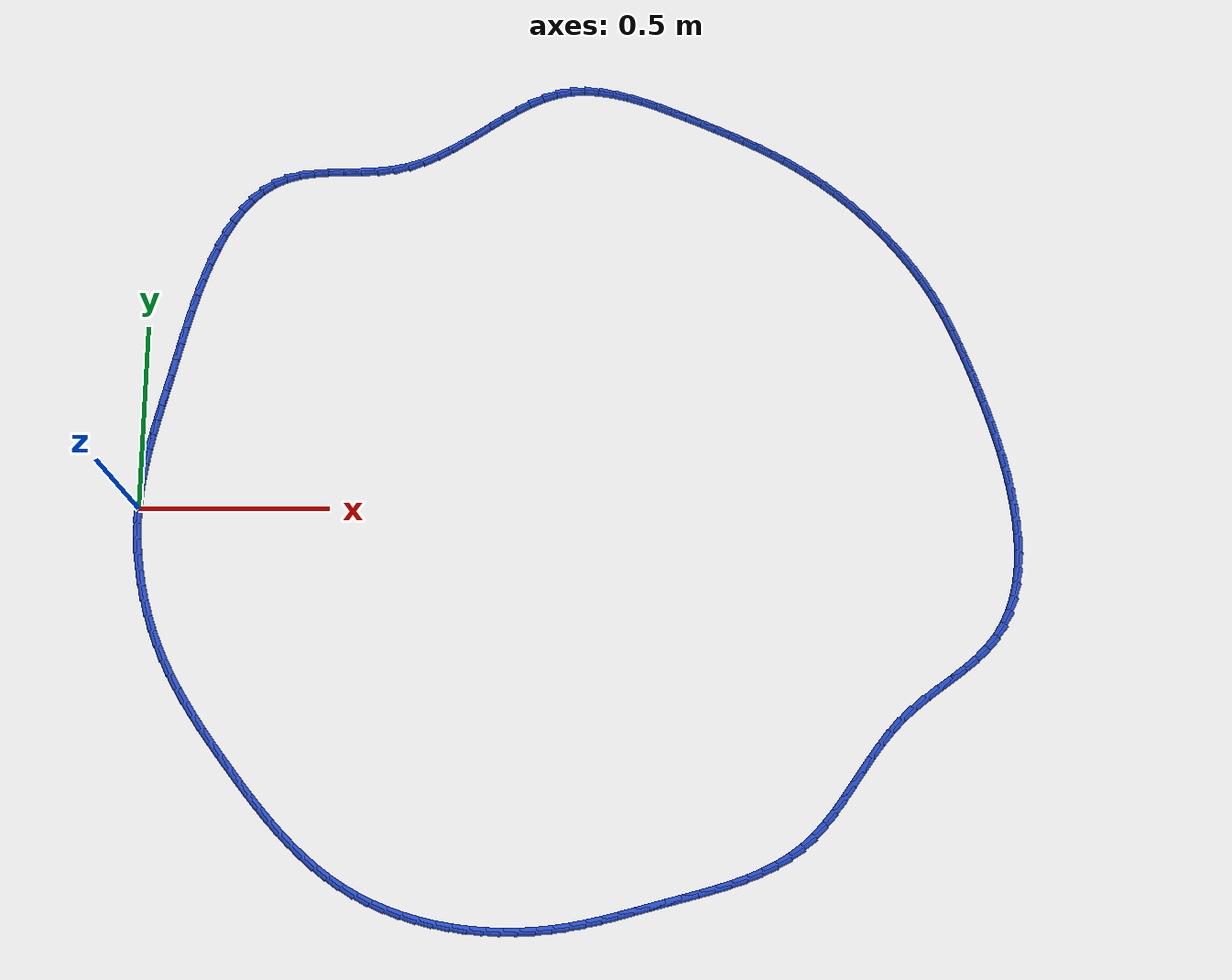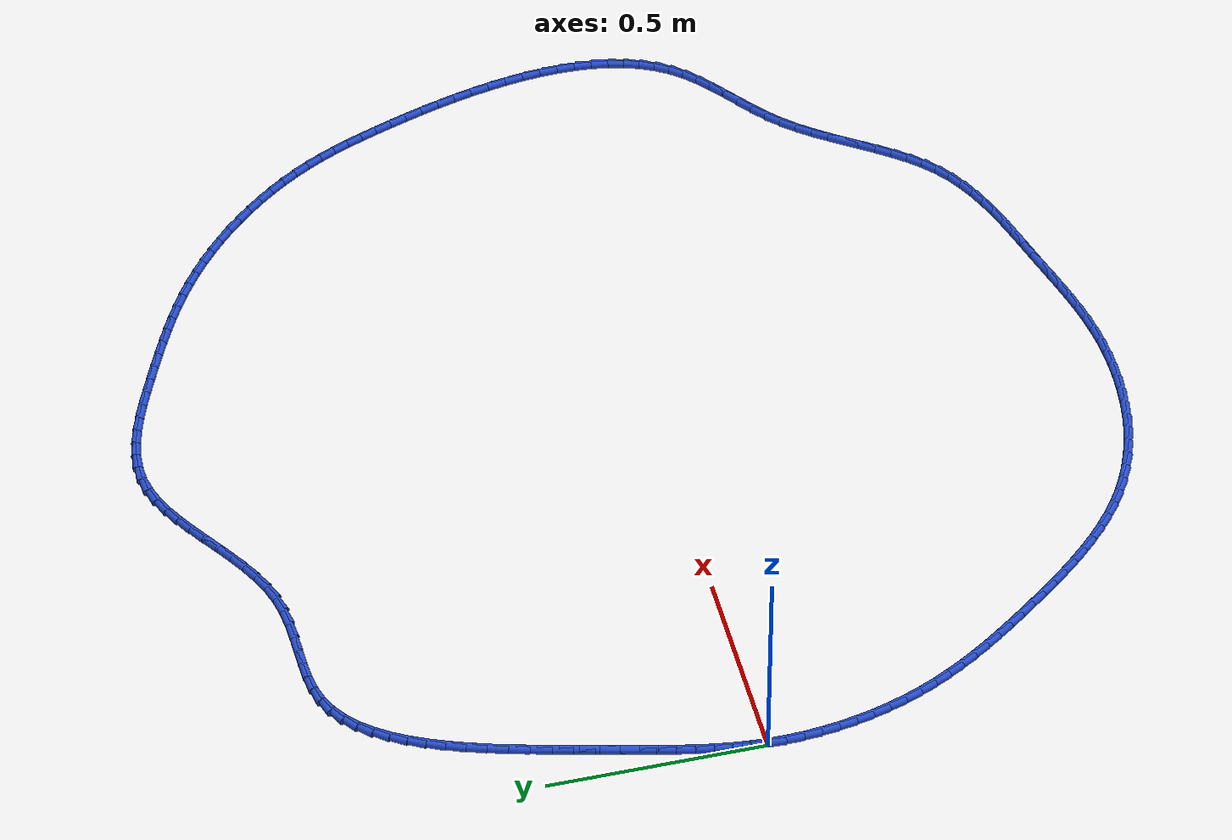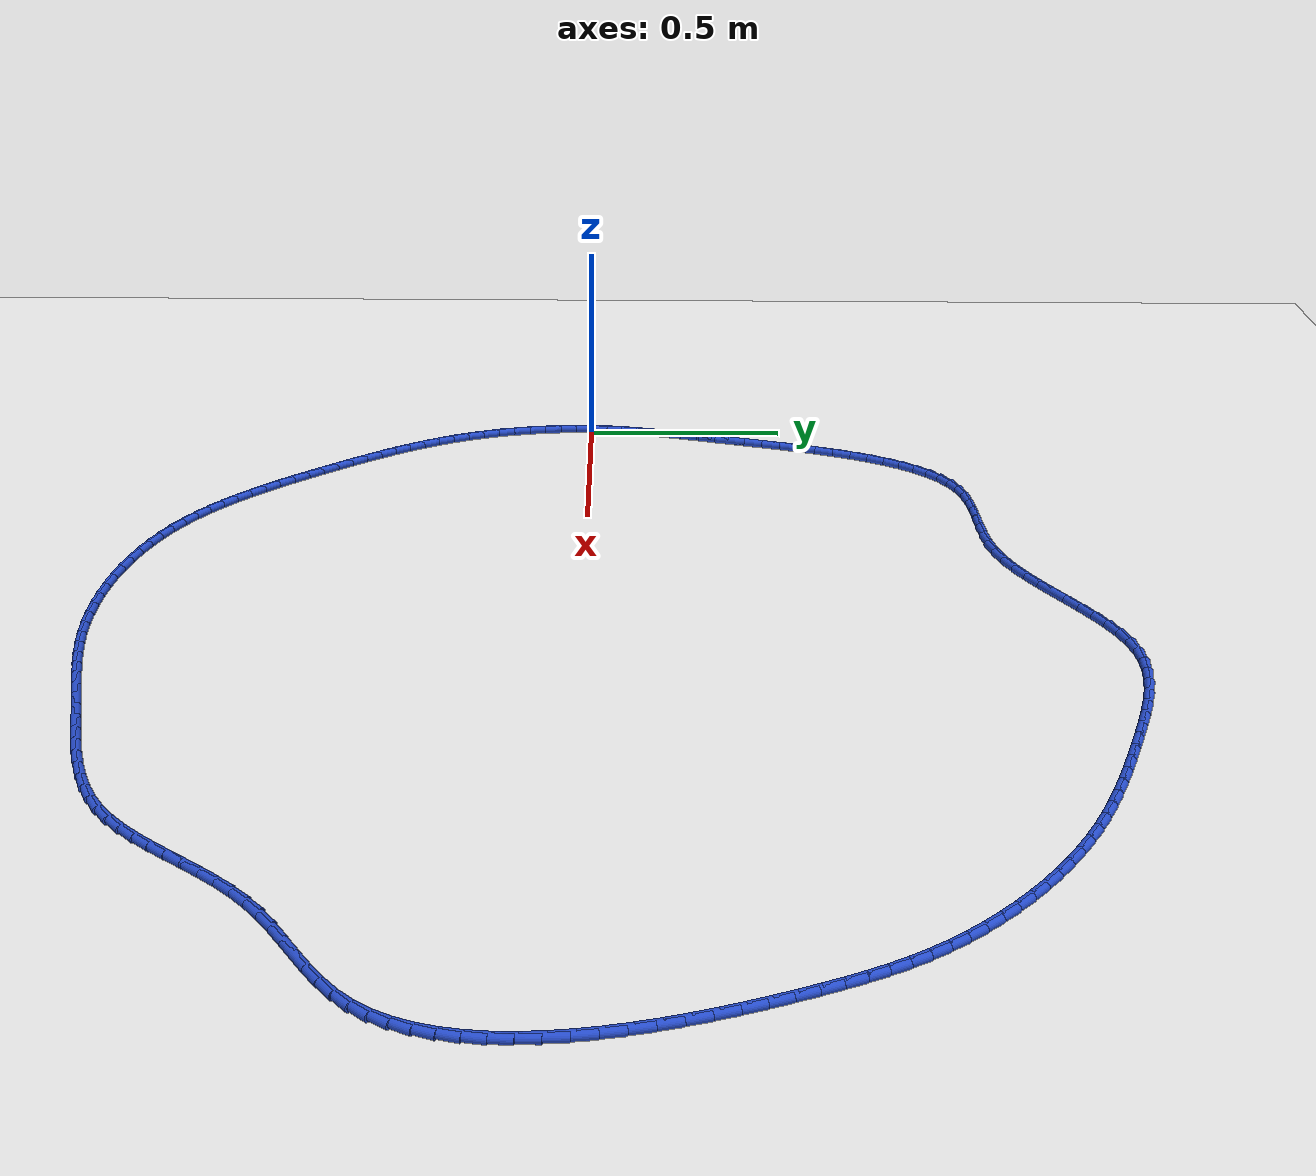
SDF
<sdf version="1.6">
 <world name="default">
  <light name="sun" type="directional">
   <pose>0 0 10 0 -0 0</pose>
   <diffuse>0.8 0.8 0.8 1</diffuse>
   <specular>0.2 0.2 0.2 1</specular>
   <attenuation>
    <range>1000</range>
    <constant>0.9</constant>
    <linear>0.01</linear>
    <quadratic>0.001</quadratic>
   </attenuation>
   <direction>-0.5 0.1 -0.9</direction>
  </light>
  <model name="ground_plane">
   <static>1</static>
   <link name="link">
    <collision name="collision">
     <geometry><plane><normal>0 0 1</normal><size>100 100</size></plane></geometry>
     <surface><friction><ode><mu>100</mu><mu2>50</mu2></ode></friction></surface>
    </collision>
    <visual name="visual">
     <cast_shadows>0</cast_shadows>
     <geometry><plane><normal>0 0 1</normal><size>100 100</size></plane></geometry>
     <material>
      <script><uri>file://media/materials/scripts/gazebo.material</uri><name>Gazebo/WhiteGlow</name></script>
     </material>
    </visual>
   </link>
  </model>
  <gravity>0 0 -9.8</gravity>
  <magnetic_field>6e-06 2.3e-05 -4.2e-05</magnetic_field>
  <atmosphere type="adiabatic"/>
  <physics name="default_physics" default="0" type="ode">
   <max_step_size>0.001</max_step_size>
   <real_time_factor>1</real_time_factor>
   <real_time_update_rate>1000</real_time_update_rate>
  </physics>
  <scene><ambient>0.4 0.4 0.4 1</ambient><background>0.7 0.7 0.7 1</background><shadows>1</shadows></scene>
  <spherical_coordinates>
   <surface_model>EARTH_WGS84</surface_model>
   <latitude_deg>0</latitude_deg>
   <longitude_deg>0</longitude_deg>
   <elevation>0</elevation>
   <heading_deg>0</heading_deg>
  </spherical_coordinates>
  <model name="line">
   <link name="link_0">
    <pose>3.469446951953614e-18 -2.0816681711721685e-17 0.01 0 1.57 1.513567746560859</pose>
    <collision name="collision">
     <geometry><cylinder><radius>0.01</radius><length>0.08</length></cylinder></geometry>
    </collision>
    <visual name="visual">
     <material>
      <script><name>Gazebo/Blue</name><uri>file://media/materials/scripts/gazebo.material</uri></script>
     </material>
     <geometry><cylinder><radius>0.01</radius><length>0.08</length></cylinder></geometry>
    </visual>
   </link>
   <link name="link_1">
    <pose>0.002307290803707648 0.0402730832526608 0.01 0 1.57 1.4660855892356623</pose>
    <collision name="collision">
     <geometry><cylinder><radius>0.01</radius><length>0.08</length></cylinder></geometry>
    </collision>
    <visual name="visual">
     <material>
      <script><name>Gazebo/Blue</name><uri>file://media/materials/scripts/gazebo.material</uri></script>
     </material>
     <geometry><cylinder><radius>0.01</radius><length>0.08</length></cylinder></geometry>
    </visual>
   </link>
   <link name="link_2">
    <pose>0.006499379447455706 0.08016160252571507 0.01 0 1.57 1.4247472507209018</pose>
    <collision name="collision">
     <geometry><cylinder><radius>0.01</radius><length>0.08</length></cylinder></geometry>
    </collision>
    <visual name="visual">
     <material>
      <script><name>Gazebo/Blue</name><uri>file://media/materials/scripts/gazebo.material</uri></script>
     </material>
     <geometry><cylinder><radius>0.01</radius><length>0.08</length></cylinder></geometry>
    </visual>
   </link>
   <link name="link_3">
    <pose>0.012342893499791058 0.11988733700476178 0.01 0 1.57 1.3902621324792257</pose>
    <collision name="collision">
     <geometry><cylinder><radius>0.01</radius><length>0.08</length></cylinder></geometry>
    </collision>
    <visual name="visual">
     <material>
      <script><name>Gazebo/Blue</name><uri>file://media/materials/scripts/gazebo.material</uri></script>
     </material>
     <geometry><cylinder><radius>0.01</radius><length>0.08</length></cylinder></geometry>
    </visual>
   </link>
   <link name="link_4">
    <pose>0.01960446052926059 0.15967206587540023 0.01 0 1.57 1.3630275392520297</pose>
    <collision name="collision">
     <geometry><cylinder><radius>0.01</radius><length>0.08</length></cylinder></geometry>
    </collision>
    <visual name="visual">
     <material>
      <script><name>Gazebo/Blue</name><uri>file://media/materials/scripts/gazebo.material</uri></script>
     </material>
     <geometry><cylinder><radius>0.01</radius><length>0.08</length></cylinder></geometry>
    </visual>
   </link>
   <link name="link_5">
    <pose>0.028050708104411192 0.19973756832322942 0.01 0 1.57 1.343162206761205</pose>
    <collision name="collision">
     <geometry><cylinder><radius>0.01</radius><length>0.08</length></cylinder></geometry>
    </collision>
    <visual name="visual">
     <material>
      <script><name>Gazebo/Blue</name><uri>file://media/materials/scripts/gazebo.material</uri></script>
     </material>
     <geometry><cylinder><radius>0.01</radius><length>0.08</length></cylinder></geometry>
    </visual>
   </link>
   <link name="link_6">
    <pose>0.037448263793789724 0.24030562353384852 0.01 0 1.57 1.3305551783907523</pose>
    <collision name="collision">
     <geometry><cylinder><radius>0.01</radius><length>0.08</length></cylinder></geometry>
    </collision>
    <visual name="visual">
     <material>
      <script><name>Gazebo/Blue</name><uri>file://media/materials/scripts/gazebo.material</uri></script>
     </material>
     <geometry><cylinder><radius>0.01</radius><length>0.08</length></cylinder></geometry>
    </visual>
   </link>
   <link name="link_7">
    <pose>0.0475637551659431 0.2815980106928566 0.01 0 1.57 1.3249169869127073</pose>
    <collision name="collision">
     <geometry><cylinder><radius>0.01</radius><length>0.08</length></cylinder></geometry>
    </collision>
    <visual name="visual">
     <material>
      <script><name>Gazebo/Blue</name><uri>file://media/materials/scripts/gazebo.material</uri></script>
     </material>
     <geometry><cylinder><radius>0.01</radius><length>0.08</length></cylinder></geometry>
    </visual>
   </link>
   <link name="link_8">
    <pose>0.05816380978941818 0.32383650898585287 0.01 0 1.57 1.3258197710168826</pose>
    <collision name="collision">
     <geometry><cylinder><radius>0.01</radius><length>0.08</length></cylinder></geometry>
    </collision>
    <visual name="visual">
     <material>
      <script><name>Gazebo/Blue</name><uri>file://media/materials/scripts/gazebo.material</uri></script>
     </material>
     <geometry><cylinder><radius>0.01</radius><length>0.08</length></cylinder></geometry>
    </visual>
   </link>
   <link name="link_9">
    <pose>0.06901523895840993 0.3672426144167921 0.01 0 1.57 1.329685726547178</pose>
    <collision name="collision">
     <geometry><cylinder><radius>0.01</radius><length>0.08</length></cylinder></geometry>
    </collision>
    <visual name="visual">
     <material>
      <script><name>Gazebo/Blue</name><uri>file://media/materials/scripts/gazebo.material</uri></script>
     </material>
     <geometry><cylinder><radius>0.01</radius><length>0.08</length></cylinder></geometry>
    </visual>
   </link>
   <link name="link_10">
    <pose>0.07999019376428974 0.4118754597198531 0.01 0 1.57 1.328282268665395</pose>
    <collision name="collision">
     <geometry><cylinder><radius>0.01</radius><length>0.08</length></cylinder></geometry>
    </collision>
    <visual name="visual">
     <material>
      <script><name>Gazebo/Blue</name><uri>file://media/materials/scripts/gazebo.material</uri></script>
     </material>
     <geometry><cylinder><radius>0.01</radius><length>0.08</length></cylinder></geometry>
    </visual>
   </link>
   <link name="link_11">
    <pose>0.09124235533844573 0.4573602472528266 0.01 0 1.57 1.3205532288843826</pose>
    <collision name="collision">
     <geometry><cylinder><radius>0.01</radius><length>0.08</length></cylinder></geometry>
    </collision>
    <visual name="visual">
     <material>
      <script><name>Gazebo/Blue</name><uri>file://media/materials/scripts/gazebo.material</uri></script>
     </material>
     <geometry><cylinder><radius>0.01</radius><length>0.08</length></cylinder></geometry>
    </visual>
   </link>
   <link name="link_12">
    <pose>0.10297193471429295 0.5032504614925318 0.01 0 1.57 1.306516507150438</pose>
    <collision name="collision">
     <geometry><cylinder><radius>0.01</radius><length>0.08</length></cylinder></geometry>
    </collision>
    <visual name="visual">
     <material>
      <script><name>Gazebo/Blue</name><uri>file://media/materials/scripts/gazebo.material</uri></script>
     </material>
     <geometry><cylinder><radius>0.01</radius><length>0.08</length></cylinder></geometry>
    </visual>
   </link>
   <link name="link_13">
    <pose>0.11537914292524641 0.5490995869157881 0.01 0 1.57 1.2858931907505875</pose>
    <collision name="collision">
     <geometry><cylinder><radius>0.01</radius><length>0.08</length></cylinder></geometry>
    </collision>
    <visual name="visual">
     <material>
      <script><name>Gazebo/Blue</name><uri>file://media/materials/scripts/gazebo.material</uri></script>
     </material>
     <geometry><cylinder><radius>0.01</radius><length>0.08</length></cylinder></geometry>
    </visual>
   </link>
   <link name="link_14">
    <pose>0.12866419100472115 0.5944611079994147 0.01 0 1.57 1.258108489723615</pose>
    <collision name="collision">
     <geometry><cylinder><radius>0.01</radius><length>0.08</length></cylinder></geometry>
    </collision>
    <visual name="visual">
     <material>
      <script><name>Gazebo/Blue</name><uri>file://media/materials/scripts/gazebo.material</uri></script>
     </material>
     <geometry><cylinder><radius>0.01</radius><length>0.08</length></cylinder></geometry>
    </visual>
   </link>
   <link name="link_15">
    <pose>0.1430272899861322 0.6388885092202309 0.01 0 1.57 1.2222717291295155</pose>
    <collision name="collision">
     <geometry><cylinder><radius>0.01</radius><length>0.08</length></cylinder></geometry>
    </collision>
    <visual name="visual">
     <material>
      <script><name>Gazebo/Blue</name><uri>file://media/materials/scripts/gazebo.material</uri></script>
     </material>
     <geometry><cylinder><radius>0.01</radius><length>0.08</length></cylinder></geometry>
    </visual>
   </link>
   <link name="link_16">
    <pose>0.15866865090289464 0.6819352750550561 0.01 0 1.57 1.1771427948496973</pose>
    <collision name="collision">
     <geometry><cylinder><radius>0.01</radius><length>0.08</length></cylinder></geometry>
    </collision>
    <visual name="visual">
     <material>
      <script><name>Gazebo/Blue</name><uri>file://media/materials/scripts/gazebo.material</uri></script>
     </material>
     <geometry><cylinder><radius>0.01</radius><length>0.08</length></cylinder></geometry>
    </visual>
   </link>
   <link name="link_17">
    <pose>0.17578848478842352 0.7231548899807095 0.01 0 1.57 1.1210986550106237</pose>
    <collision name="collision">
     <geometry><cylinder><radius>0.01</radius><length>0.08</length></cylinder></geometry>
    </collision>
    <visual name="visual">
     <material>
      <script><name>Gazebo/Blue</name><uri>file://media/materials/scripts/gazebo.material</uri></script>
     </material>
     <geometry><cylinder><radius>0.01</radius><length>0.08</length></cylinder></geometry>
    </visual>
   </link>
   <link name="link_18">
    <pose>0.1945870026761337 0.7621008384740104 0.01 0 1.57 1.0521294883734549</pose>
    <collision name="collision">
     <geometry><cylinder><radius>0.01</radius><length>0.08</length></cylinder></geometry>
    </collision>
    <visual name="visual">
     <material>
      <script><name>Gazebo/Blue</name><uri>file://media/materials/scripts/gazebo.material</uri></script>
     </material>
     <geometry><cylinder><radius>0.01</radius><length>0.08</length></cylinder></geometry>
    </visual>
   </link>
   <link name="link_19">
    <pose>0.21526441559944043 0.7983266050117783 0.01 0 1.57 0.9679256834273765</pose>
    <collision name="collision">
     <geometry><cylinder><radius>0.01</radius><length>0.08</length></cylinder></geometry>
    </collision>
    <visual name="visual">
     <material>
      <script><name>Gazebo/Blue</name><uri>file://media/materials/scripts/gazebo.material</uri></script>
     </material>
     <geometry><cylinder><radius>0.01</radius><length>0.08</length></cylinder></geometry>
    </visual>
   </link>
   <link name="link_20">
    <pose>0.23802093459175883 0.8313856740708325 0.01 0 1.57 0.8661670576618331</pose>
    <collision name="collision">
     <geometry><cylinder><radius>0.01</radius><length>0.08</length></cylinder></geometry>
    </collision>
    <visual name="visual">
     <material>
      <script><name>Gazebo/Blue</name><uri>file://media/materials/scripts/gazebo.material</uri></script>
     </material>
     <geometry><cylinder><radius>0.01</radius><length>0.08</length></cylinder></geometry>
    </visual>
   </link>
   <link name="link_21">
    <pose>0.26305677068650357 0.8608315301279919 0.01 0 1.57 0.7451707905215994</pose>
    <collision name="collision">
     <geometry><cylinder><radius>0.01</radius><length>0.08</length></cylinder></geometry>
    </collision>
    <visual name="visual">
     <material>
      <script><name>Gazebo/Blue</name><uri>file://media/materials/scripts/gazebo.material</uri></script>
     </material>
     <geometry><cylinder><radius>0.01</radius><length>0.08</length></cylinder></geometry>
    </visual>
   </link>
   <link name="link_22">
    <pose>0.2905721349170899 0.886217657660076 0.01 0 1.57 0.6049977734661363</pose>
    <collision name="collision">
     <geometry><cylinder><radius>0.01</radius><length>0.08</length></cylinder></geometry>
    </collision>
    <visual name="visual">
     <material>
      <script><name>Gazebo/Blue</name><uri>file://media/materials/scripts/gazebo.material</uri></script>
     </material>
     <geometry><cylinder><radius>0.01</radius><length>0.08</length></cylinder></geometry>
    </visual>
   </link>
   <link name="link_23">
    <pose>0.32076723831693293 0.9070975411439043 0.01 0 1.57 0.4487748392204587</pose>
    <collision name="collision">
     <geometry><cylinder><radius>0.01</radius><length>0.08</length></cylinder></geometry>
    </collision>
    <visual name="visual">
     <material>
      <script><name>Gazebo/Blue</name><uri>file://media/materials/scripts/gazebo.material</uri></script>
     </material>
     <geometry><cylinder><radius>0.01</radius><length>0.08</length></cylinder></geometry>
    </visual>
   </link>
   <link name="link_24">
    <pose>0.3538422919194476 0.9230246650562957 0.01 0 1.57 0.28764588681178777</pose>
    <collision name="collision">
     <geometry><cylinder><radius>0.01</radius><length>0.08</length></cylinder></geometry>
    </collision>
    <visual name="visual">
     <material>
      <script><name>Gazebo/Blue</name><uri>file://media/materials/scripts/gazebo.material</uri></script>
     </material>
     <geometry><cylinder><radius>0.01</radius><length>0.08</length></cylinder></geometry>
    </visual>
   </link>
   <link name="link_25">
    <pose>0.3899305413883094 0.9337014037659046 0.01 0 1.57 0.16021983275278942</pose>
    <collision name="collision">
     <geometry><cylinder><radius>0.01</radius><length>0.08</length></cylinder></geometry>
    </collision>
    <visual name="visual">
     <material>
      <script><name>Gazebo/Blue</name><uri>file://media/materials/scripts/gazebo.material</uri></script>
     </material>
     <geometry><cylinder><radius>0.01</radius><length>0.08</length></cylinder></geometry>
    </visual>
   </link>
   <link name="link_26">
    <pose>0.4286571402405392 0.9399598168062934 0.01 0 1.57 0.07811345998192167</pose>
    <collision name="collision">
     <geometry><cylinder><radius>0.01</radius><length>0.08</length></cylinder></geometry>
    </collision>
    <visual name="visual">
     <material>
      <script><name>Gazebo/Blue</name><uri>file://media/materials/scripts/gazebo.material</uri></script>
     </material>
     <geometry><cylinder><radius>0.01</radius><length>0.08</length></cylinder></geometry>
    </visual>
   </link>
   <link name="link_27">
    <pose>0.46941425353159494 0.9431499870860284 0.01 0 1.57 0.03494937340459771</pose>
    <collision name="collision">
     <geometry><cylinder><radius>0.01</radius><length>0.08</length></cylinder></geometry>
    </collision>
    <visual name="visual">
     <material>
      <script><name>Gazebo/Blue</name><uri>file://media/materials/scripts/gazebo.material</uri></script>
     </material>
     <geometry><cylinder><radius>0.01</radius><length>0.08</length></cylinder></geometry>
    </visual>
   </link>
   <link name="link_28">
    <pose>0.5115928297644247 0.9446247023799725 0.01 0 1.57 0.025861237856905785</pose>
    <collision name="collision">
     <geometry><cylinder><radius>0.01</radius><length>0.08</length></cylinder></geometry>
    </collision>
    <visual name="visual">
     <material>
      <script><name>Gazebo/Blue</name><uri>file://media/materials/scripts/gazebo.material</uri></script>
     </material>
     <geometry><cylinder><radius>0.01</radius><length>0.08</length></cylinder></geometry>
    </visual>
   </link>
   <link name="link_29">
    <pose>0.5545838174419758 0.9457367504629886 0.01 0 1.57 0.04862930973185276</pose>
    <collision name="collision">
     <geometry><cylinder><radius>0.01</radius><length>0.08</length></cylinder></geometry>
    </collision>
    <visual name="visual">
     <material>
      <script><name>Gazebo/Blue</name><uri>file://media/materials/scripts/gazebo.material</uri></script>
     </material>
     <geometry><cylinder><radius>0.01</radius><length>0.08</length></cylinder></geometry>
    </visual>
   </link>
   <link name="link_30">
    <pose>0.5977781650671959 0.9478389191099389 0.01 0 1.57 0.10351316778377101</pose>
    <collision name="collision">
     <geometry><cylinder><radius>0.01</radius><length>0.08</length></cylinder></geometry>
    </collision>
    <visual name="visual">
     <material>
      <script><name>Gazebo/Blue</name><uri>file://media/materials/scripts/gazebo.material</uri></script>
     </material>
     <geometry><cylinder><radius>0.01</radius><length>0.08</length></cylinder></geometry>
    </visual>
   </link>
   <link name="link_31">
    <pose>0.6405668211430333 0.9522839960956866 0.01 0 1.57 0.19246012140656626</pose>
    <collision name="collision">
     <geometry><cylinder><radius>0.01</radius><length>0.08</length></cylinder></geometry>
    </collision>
    <visual name="visual">
     <material>
      <script><name>Gazebo/Blue</name><uri>file://media/materials/scripts/gazebo.material</uri></script>
     </material>
     <geometry><cylinder><radius>0.01</radius><length>0.08</length></cylinder></geometry>
    </visual>
   </link>
   <link name="link_32">
    <pose>0.6823408036860743 0.9604245824730442 0.01 0 1.57 0.3055809782618776</pose>
    <collision name="collision">
     <geometry><cylinder><radius>0.01</radius><length>0.08</length></cylinder></geometry>
    </collision>
    <visual name="visual">
     <material>
      <script><name>Gazebo/Blue</name><uri>file://media/materials/scripts/gazebo.material</uri></script>
     </material>
     <geometry><cylinder><radius>0.01</radius><length>0.08</length></cylinder></geometry>
    </visual>
   </link>
   <link name="link_33">
    <pose>0.7226653048711963 0.9731454264169739 0.01 0 1.57 0.40487203242769426</pose>
    <collision name="collision">
     <geometry><cylinder><radius>0.01</radius><length>0.08</length></cylinder></geometry>
    </collision>
    <visual name="visual">
     <material>
      <script><name>Gazebo/Blue</name><uri>file://media/materials/scripts/gazebo.material</uri></script>
     </material>
     <geometry><cylinder><radius>0.01</radius><length>0.08</length></cylinder></geometry>
    </visual>
   </link>
   <link name="link_34">
    <pose>0.7616552933825825 0.9898545098325305 0.01 0 1.57 0.4819630412846346</pose>
    <collision name="collision">
     <geometry><cylinder><radius>0.01</radius><length>0.08</length></cylinder></geometry>
    </collision>
    <visual name="visual">
     <material>
      <script><name>Gazebo/Blue</name><uri>file://media/materials/scripts/gazebo.material</uri></script>
     </material>
     <geometry><cylinder><radius>0.01</radius><length>0.08</length></cylinder></geometry>
    </visual>
   </link>
   <link name="link_35">
    <pose>0.7995339459274257 1.0096691547733416 0.01 0 1.57 0.537297461957851</pose>
    <collision name="collision">
     <geometry><cylinder><radius>0.01</radius><length>0.08</length></cylinder></geometry>
    </collision>
    <visual name="visual">
     <material>
      <script><name>Gazebo/Blue</name><uri>file://media/materials/scripts/gazebo.material</uri></script>
     </material>
     <geometry><cylinder><radius>0.01</radius><length>0.08</length></cylinder></geometry>
    </visual>
   </link>
   <link name="link_36">
    <pose>0.8365244392129185 1.031706683293035 0.01 0 1.57 0.5718363714529956</pose>
    <collision name="collision">
     <geometry><cylinder><radius>0.01</radius><length>0.08</length></cylinder></geometry>
    </collision>
    <visual name="visual">
     <material>
      <script><name>Gazebo/Blue</name><uri>file://media/materials/scripts/gazebo.material</uri></script>
     </material>
     <geometry><cylinder><radius>0.01</radius><length>0.08</length></cylinder></geometry>
    </visual>
   </link>
   <link name="link_37">
    <pose>0.8728499499462534 1.0550844174452383 0.01 0 1.57 0.5863182019594531</pose>
    <collision name="collision">
     <geometry><cylinder><radius>0.01</radius><length>0.08</length></cylinder></geometry>
    </collision>
    <visual name="visual">
     <material>
      <script><name>Gazebo/Blue</name><uri>file://media/materials/scripts/gazebo.material</uri></script>
     </material>
     <geometry><cylinder><radius>0.01</radius><length>0.08</length></cylinder></geometry>
    </visual>
   </link>
   <link name="link_38">
    <pose>0.9087336548346232 1.0789196792835785 0.01 0 1.57 0.5808524894237596</pose>
    <collision name="collision">
     <geometry><cylinder><radius>0.01</radius><length>0.08</length></cylinder></geometry>
    </collision>
    <visual name="visual">
     <material>
      <script><name>Gazebo/Blue</name><uri>file://media/materials/scripts/gazebo.material</uri></script>
     </material>
     <geometry><cylinder><radius>0.01</radius><length>0.08</length></cylinder></geometry>
    </visual>
   </link>
   <link name="link_39">
    <pose>0.9443987305852202 1.1023297908616836 0.01 0 1.57 0.5547347937019425</pose>
    <collision name="collision">
     <geometry><cylinder><radius>0.01</radius><length>0.08</length></cylinder></geometry>
    </collision>
    <visual name="visual">
     <material>
      <script><name>Gazebo/Blue</name><uri>file://media/materials/scripts/gazebo.material</uri></script>
     </material>
     <geometry><cylinder><radius>0.01</radius><length>0.08</length></cylinder></geometry>
    </visual>
   </link>
   <link name="link_40">
    <pose>0.9800683539052372 1.1244320742331806 0.01 0 1.57 0.5064342362517487</pose>
    <collision name="collision">
     <geometry><cylinder><radius>0.01</radius><length>0.08</length></cylinder></geometry>
    </collision>
    <visual name="visual">
     <material>
      <script><name>Gazebo/Blue</name><uri>file://media/materials/scripts/gazebo.material</uri></script>
     </material>
     <geometry><cylinder><radius>0.01</radius><length>0.08</length></cylinder></geometry>
    </visual>
   </link>
   <link name="link_41">
    <pose>1.0159657015018666 1.1443438514516973 0.01 0 1.57 0.43382387891929614</pose>
    <collision name="collision">
     <geometry><cylinder><radius>0.01</radius><length>0.08</length></cylinder></geometry>
    </collision>
    <visual name="visual">
     <material>
      <script><name>Gazebo/Blue</name><uri>file://media/materials/scripts/gazebo.material</uri></script>
     </material>
     <geometry><cylinder><radius>0.01</radius><length>0.08</length></cylinder></geometry>
    </visual>
   </link>
   <link name="link_42">
    <pose>1.0523139500823013 1.1611824445708614 0.01 0 1.57 0.33486695225909147</pose>
    <collision name="collision">
     <geometry><cylinder><radius>0.01</radius><length>0.08</length></cylinder></geometry>
    </collision>
    <visual name="visual">
     <material>
      <script><name>Gazebo/Blue</name><uri>file://media/materials/scripts/gazebo.material</uri></script>
     </material>
     <geometry><cylinder><radius>0.01</radius><length>0.08</length></cylinder></geometry>
    </visual>
   </link>
   <link name="link_43">
    <pose>1.0893362763537335 1.1740651756443001 0.01 0 1.57 0.20904646533501528</pose>
    <collision name="collision">
     <geometry><cylinder><radius>0.01</radius><length>0.08</length></cylinder></geometry>
    </collision>
    <visual name="visual">
     <material>
      <script><name>Gazebo/Blue</name><uri>file://media/materials/scripts/gazebo.material</uri></script>
     </material>
     <geometry><cylinder><radius>0.01</radius><length>0.08</length></cylinder></geometry>
    </visual>
   </link>
   <link name="link_44">
    <pose>1.127255780302199 1.1821096388863792 0.01 0 1.57 0.06854633437691574</pose>
    <collision name="collision">
     <geometry><cylinder><radius>0.01</radius><length>0.08</length></cylinder></geometry>
    </collision>
    <visual name="visual">
     <material>
      <script><name>Gazebo/Blue</name><uri>file://media/materials/scripts/gazebo.material</uri></script>
     </material>
     <geometry><cylinder><radius>0.01</radius><length>0.08</length></cylinder></geometry>
    </visual>
   </link>
   <link name="link_45">
    <pose>1.1661969894721655 1.18478310452521 0.01 0 1.57 -0.05509741451226116</pose>
    <collision name="collision">
     <geometry><cylinder><radius>0.01</radius><length>0.08</length></cylinder></geometry>
    </collision>
    <visual name="visual">
     <material>
      <script><name>Gazebo/Blue</name><uri>file://media/materials/scripts/gazebo.material</uri></script>
     </material>
     <geometry><cylinder><radius>0.01</radius><length>0.08</length></cylinder></geometry>
    </visual>
   </link>
   <link name="link_46">
    <pose>1.20599255363776 1.182588250389758 0.01 0 1.57 -0.15627035638043646</pose>
    <collision name="collision">
     <geometry><cylinder><radius>0.01</radius><length>0.08</length></cylinder></geometry>
    </collision>
    <visual name="visual">
     <material>
      <script><name>Gazebo/Blue</name><uri>file://media/materials/scripts/gazebo.material</uri></script>
     </material>
     <geometry><cylinder><radius>0.01</radius><length>0.08</length></cylinder></geometry>
    </visual>
   </link>
   <link name="link_47">
    <pose>1.2464213542993945 1.1762184919565535 0.01 0 1.57 -0.23668898038604896</pose>
    <collision name="collision">
     <geometry><cylinder><radius>0.01</radius><length>0.08</length></cylinder></geometry>
    </collision>
    <visual name="visual">
     <material>
      <script><name>Gazebo/Blue</name><uri>file://media/materials/scripts/gazebo.material</uri></script>
     </material>
     <geometry><cylinder><radius>0.01</radius><length>0.08</length></cylinder></geometry>
    </visual>
   </link>
   <link name="link_48">
    <pose>1.2872622729574785 1.1663672447021258 0.01 0 1.57 -0.29881315057976904</pose>
    <collision name="collision">
     <geometry><cylinder><radius>0.01</radius><length>0.08</length></cylinder></geometry>
    </collision>
    <visual name="visual">
     <material>
      <script><name>Gazebo/Blue</name><uri>file://media/materials/scripts/gazebo.material</uri></script>
     </material>
     <geometry><cylinder><radius>0.01</radius><length>0.08</length></cylinder></geometry>
    </visual>
   </link>
   <link name="link_49">
    <pose>1.328294191112424 1.1537279241030047 0.01 0 1.57 -0.34497964643754225</pose>
    <collision name="collision">
     <geometry><cylinder><radius>0.01</radius><length>0.08</length></cylinder></geometry>
    </collision>
    <visual name="visual">
     <material>
      <script><name>Gazebo/Blue</name><uri>file://media/materials/scripts/gazebo.material</uri></script>
     </material>
     <geometry><cylinder><radius>0.01</radius><length>0.08</length></cylinder></geometry>
    </visual>
   </link>
   <link name="link_50">
    <pose>1.3692959902646415 1.1389939456357197 0.01 0 1.57 -0.37701089247184477</pose>
    <collision name="collision">
     <geometry><cylinder><radius>0.01</radius><length>0.08</length></cylinder></geometry>
    </collision>
    <visual name="visual">
     <material>
      <script><name>Gazebo/Blue</name><uri>file://media/materials/scripts/gazebo.material</uri></script>
     </material>
     <geometry><cylinder><radius>0.01</radius><length>0.08</length></cylinder></geometry>
    </visual>
   </link>
   <link name="link_51">
    <pose>1.4100465519145418 1.1228587247768016 0.01 0 1.57 -0.396069491498876</pose>
    <collision name="collision">
     <geometry><cylinder><radius>0.01</radius><length>0.08</length></cylinder></geometry>
    </collision>
    <visual name="visual">
     <material>
      <script><name>Gazebo/Blue</name><uri>file://media/materials/scripts/gazebo.material</uri></script>
     </material>
     <geometry><cylinder><radius>0.01</radius><length>0.08</length></cylinder></geometry>
    </visual>
   </link>
   <link name="link_52">
    <pose>1.4503247575625364 1.1060156770027791 0.01 0 1.57 -0.4037262229836692</pose>
    <collision name="collision">
     <geometry><cylinder><radius>0.01</radius><length>0.08</length></cylinder></geometry>
    </collision>
    <visual name="visual">
     <material>
      <script><name>Gazebo/Blue</name><uri>file://media/materials/scripts/gazebo.material</uri></script>
     </material>
     <geometry><cylinder><radius>0.01</radius><length>0.08</length></cylinder></geometry>
    </visual>
   </link>
   <link name="link_53">
    <pose>1.4899256579240476 1.0890984705465996 0.01 0 1.57 -0.41035904107302573</pose>
    <collision name="collision">
     <geometry><cylinder><radius>0.01</radius><length>0.08</length></cylinder></geometry>
    </collision>
    <visual name="visual">
     <material>
      <script><name>Gazebo/Blue</name><uri>file://media/materials/scripts/gazebo.material</uri></script>
     </material>
     <geometry><cylinder><radius>0.01</radius><length>0.08</length></cylinder></geometry>
    </visual>
   </link>
   <link name="link_54">
    <pose>1.5287937378391696 1.0721885961211908 0.01 0 1.57 -0.42170604757677266</pose>
    <collision name="collision">
     <geometry><cylinder><radius>0.01</radius><length>0.08</length></cylinder></geometry>
    </collision>
    <visual name="visual">
     <material>
      <script><name>Gazebo/Blue</name><uri>file://media/materials/scripts/gazebo.material</uri></script>
     </material>
     <geometry><cylinder><radius>0.01</radius><length>0.08</length></cylinder></geometry>
    </visual>
   </link>
   <link name="link_55">
    <pose>1.566954276156908 1.0550690006124168 0.01 0 1.57 -0.4379204622202308</pose>
    <collision name="collision">
     <geometry><cylinder><radius>0.01</radius><length>0.08</length></cylinder></geometry>
    </collision>
    <visual name="visual">
     <material>
      <script><name>Gazebo/Blue</name><uri>file://media/materials/scripts/gazebo.material</uri></script>
     </material>
     <geometry><cylinder><radius>0.01</radius><length>0.08</length></cylinder></geometry>
    </visual>
   </link>
   <link name="link_56">
    <pose>1.6044333433577622 1.037519705730133 0.01 0 1.57 -0.459012491445624</pose>
    <collision name="collision">
     <geometry><cylinder><radius>0.01</radius><length>0.08</length></cylinder></geometry>
    </collision>
    <visual name="visual">
     <material>
      <script><name>Gazebo/Blue</name><uri>file://media/materials/scripts/gazebo.material</uri></script>
     </material>
     <geometry><cylinder><radius>0.01</radius><length>0.08</length></cylinder></geometry>
    </visual>
   </link>
   <link name="link_57">
    <pose>1.6412570099222341 1.0193207331841945 0.01 0 1.57 -0.4848884323864052</pose>
    <collision name="collision">
     <geometry><cylinder><radius>0.01</radius><length>0.08</length></cylinder></geometry>
    </collision>
    <visual name="visual">
     <material>
      <script><name>Gazebo/Blue</name><uri>file://media/materials/scripts/gazebo.material</uri></script>
     </material>
     <geometry><cylinder><radius>0.01</radius><length>0.08</length></cylinder></geometry>
    </visual>
   </link>
   <link name="link_58">
    <pose>1.6774513463308263 1.000252104684457 0.01 0 1.57 -0.5153360059701494</pose>
    <collision name="collision">
     <geometry><cylinder><radius>0.01</radius><length>0.08</length></cylinder></geometry>
    </collision>
    <visual name="visual">
     <material>
      <script><name>Gazebo/Blue</name><uri>file://media/materials/scripts/gazebo.material</uri></script>
     </material>
     <geometry><cylinder><radius>0.01</radius><length>0.08</length></cylinder></geometry>
    </visual>
   </link>
   <link name="link_59">
    <pose>1.713042423064037 0.9800938419407756 0.01 0 1.57 -0.550014079441732</pose>
    <collision name="collision">
     <geometry><cylinder><radius>0.01</radius><length>0.08</length></cylinder></geometry>
    </collision>
    <visual name="visual">
     <material>
      <script><name>Gazebo/Blue</name><uri>file://media/materials/scripts/gazebo.material</uri></script>
     </material>
     <geometry><cylinder><radius>0.01</radius><length>0.08</length></cylinder></geometry>
    </visual>
   </link>
   <link name="link_60">
    <pose>1.7480563106023688 0.9586259666630057 0.01 0 1.57 -0.5879182547053827</pose>
    <collision name="collision">
     <geometry><cylinder><radius>0.01</radius><length>0.08</length></cylinder></geometry>
    </collision>
    <visual name="visual">
     <material>
      <script><name>Gazebo/Blue</name><uri>file://media/materials/scripts/gazebo.material</uri></script>
     </material>
     <geometry><cylinder><radius>0.01</radius><length>0.08</length></cylinder></geometry>
    </visual>
   </link>
   <link name="link_61">
    <pose>1.7825024693280276 0.9356660574340228 0.01 0 1.57 -0.6260137774116261</pose>
    <collision name="collision">
     <geometry><cylinder><radius>0.01</radius><length>0.08</length></cylinder></geometry>
    </collision>
    <visual name="visual">
     <material>
      <script><name>Gazebo/Blue</name><uri>file://media/materials/scripts/gazebo.material</uri></script>
     </material>
     <geometry><cylinder><radius>0.01</radius><length>0.08</length></cylinder></geometry>
    </visual>
   </link>
   <link name="link_62">
    <pose>1.8163042102024922 0.9112264841496295 0.01 0 1.57 -0.663605238005424</pose>
    <collision name="collision">
     <geometry><cylinder><radius>0.01</radius><length>0.08</length></cylinder></geometry>
    </collision>
    <visual name="visual">
     <material>
      <script><name>Gazebo/Blue</name><uri>file://media/materials/scripts/gazebo.material</uri></script>
     </material>
     <geometry><cylinder><radius>0.01</radius><length>0.08</length></cylinder></geometry>
    </visual>
   </link>
   <link name="link_63">
    <pose>1.84935699972535 0.8853825754492208 0.01 0 1.57 -0.7009402538940767</pose>
    <collision name="collision">
     <geometry><cylinder><radius>0.01</radius><length>0.08</length></cylinder></geometry>
    </collision>
    <visual name="visual">
     <material>
      <script><name>Gazebo/Blue</name><uri>file://media/materials/scripts/gazebo.material</uri></script>
     </material>
     <geometry><cylinder><radius>0.01</radius><length>0.08</length></cylinder></geometry>
    </visual>
   </link>
   <link name="link_64">
    <pose>1.881556290441462 0.8582096915250351 0.01 0 1.57 -0.7382594551700933</pose>
    <collision name="collision">
     <geometry><cylinder><radius>0.01</radius><length>0.08</length></cylinder></geometry>
    </collision>
    <visual name="visual">
     <material>
      <script><name>Gazebo/Blue</name><uri>file://media/materials/scripts/gazebo.material</uri></script>
     </material>
     <geometry><cylinder><radius>0.01</radius><length>0.08</length></cylinder></geometry>
    </visual>
   </link>
   <link name="link_65">
    <pose>1.9127975348956903 0.8297831925693105 0.01 0 1.57 -0.7757988553789479</pose>
    <collision name="collision">
     <geometry><cylinder><radius>0.01</radius><length>0.08</length></cylinder></geometry>
    </collision>
    <visual name="visual">
     <material>
      <script><name>Gazebo/Blue</name><uri>file://media/materials/scripts/gazebo.material</uri></script>
     </material>
     <geometry><cylinder><radius>0.01</radius><length>0.08</length></cylinder></geometry>
    </visual>
   </link>
   <link name="link_66">
    <pose>1.9429761856328966 0.8001784387742845 0.01 0 1.57 -0.8137924522642171</pose>
    <collision name="collision">
     <geometry><cylinder><radius>0.01</radius><length>0.08</length></cylinder></geometry>
    </collision>
    <visual name="visual">
     <material>
      <script><name>Gazebo/Blue</name><uri>file://media/materials/scripts/gazebo.material</uri></script>
     </material>
     <geometry><cylinder><radius>0.01</radius><length>0.08</length></cylinder></geometry>
    </visual>
   </link>
   <link name="link_67">
    <pose>1.9719876951979434 0.7694707903321962 0.01 0 1.57 -0.8524745462738602</pose>
    <collision name="collision">
     <geometry><cylinder><radius>0.01</radius><length>0.08</length></cylinder></geometry>
    </collision>
    <visual name="visual">
     <material>
      <script><name>Gazebo/Blue</name><uri>file://media/materials/scripts/gazebo.material</uri></script>
     </material>
     <geometry><cylinder><radius>0.01</radius><length>0.08</length></cylinder></geometry>
    </visual>
   </link>
   <link name="link_68">
    <pose>1.9997275161356913 0.7377356074352831 0.01 0 1.57 -0.8920816944253648</pose>
    <collision name="collision">
     <geometry><cylinder><radius>0.01</radius><length>0.08</length></cylinder></geometry>
    </collision>
    <visual name="visual">
     <material>
      <script><name>Gazebo/Blue</name><uri>file://media/materials/scripts/gazebo.material</uri></script>
     </material>
     <geometry><cylinder><radius>0.01</radius><length>0.08</length></cylinder></geometry>
    </visual>
   </link>
   <link name="link_69">
    <pose>2.026091100991002 0.7050482502757833 0.01 0 1.57 -0.9328541848154398</pose>
    <collision name="collision">
     <geometry><cylinder><radius>0.01</radius><length>0.08</length></cylinder></geometry>
    </collision>
    <visual name="visual">
     <material>
      <script><name>Gazebo/Blue</name><uri>file://media/materials/scripts/gazebo.material</uri></script>
     </material>
     <geometry><cylinder><radius>0.01</radius><length>0.08</length></cylinder></geometry>
    </visual>
   </link>
   <link name="link_70">
    <pose>2.0509739023087374 0.6714840790459354 0.01 0 1.57 -0.975036869855163</pose>
    <collision name="collision">
     <geometry><cylinder><radius>0.01</radius><length>0.08</length></cylinder></geometry>
    </collision>
    <visual name="visual">
     <material>
      <script><name>Gazebo/Blue</name><uri>file://media/materials/scripts/gazebo.material</uri></script>
     </material>
     <geometry><cylinder><radius>0.01</radius><length>0.08</length></cylinder></geometry>
    </visual>
   </link>
   <link name="link_71">
    <pose>2.07427137263376 0.637118453937977 0.01 0 1.57 -1.0188791342013779</pose>
    <collision name="collision">
     <geometry><cylinder><radius>0.01</radius><length>0.08</length></cylinder></geometry>
    </collision>
    <visual name="visual">
     <material>
      <script><name>Gazebo/Blue</name><uri>file://media/materials/scripts/gazebo.material</uri></script>
     </material>
     <geometry><cylinder><radius>0.01</radius><length>0.08</length></cylinder></geometry>
    </visual>
   </link>
   <link name="link_72">
    <pose>2.095878964510931 0.6020267351441467 0.01 0 1.57 -1.0643881370935382</pose>
    <collision name="collision">
     <geometry><cylinder><radius>0.01</radius><length>0.08</length></cylinder></geometry>
    </collision>
    <visual name="visual">
     <material>
      <script><name>Gazebo/Blue</name><uri>file://media/materials/scripts/gazebo.material</uri></script>
     </material>
     <geometry><cylinder><radius>0.01</radius><length>0.08</length></cylinder></geometry>
    </visual>
   </link>
   <link name="link_73">
    <pose>2.115708238392594 0.5662759309592335 0.01 0 1.57 -1.107677617199653</pose>
    <collision name="collision">
     <geometry><cylinder><radius>0.01</radius><length>0.08</length></cylinder></geometry>
    </collision>
    <visual name="visual">
     <material>
      <script><name>Gazebo/Blue</name><uri>file://media/materials/scripts/gazebo.material</uri></script>
     </material>
     <geometry><cylinder><radius>0.01</radius><length>0.08</length></cylinder></geometry>
    </visual>
   </link>
   <link name="link_74">
    <pose>2.1339202553462244 0.5298036844235112 0.01 0 1.57 -1.1448025772364245</pose>
    <collision name="collision">
     <geometry><cylinder><radius>0.01</radius><length>0.08</length></cylinder></geometry>
    </collision>
    <visual name="visual">
     <material>
      <script><name>Gazebo/Blue</name><uri>file://media/materials/scripts/gazebo.material</uri></script>
     </material>
     <geometry><cylinder><radius>0.01</radius><length>0.08</length></cylinder></geometry>
    </visual>
   </link>
   <link name="link_75">
    <pose>2.1508725733797767 0.49244575555503317 0.01 0 1.57 -1.1748727489428332</pose>
    <collision name="collision">
     <geometry><cylinder><radius>0.01</radius><length>0.08</length></cylinder></geometry>
    </collision>
    <visual name="visual">
     <material>
      <script><name>Gazebo/Blue</name><uri>file://media/materials/scripts/gazebo.material</uri></script>
     </material>
     <geometry><cylinder><radius>0.01</radius><length>0.08</length></cylinder></geometry>
    </visual>
   </link>
   <link name="link_76">
    <pose>2.1669280677893346 0.4540351473753115 0.01 0 1.57 -1.1975013346610845</pose>
    <collision name="collision">
     <geometry><cylinder><radius>0.01</radius><length>0.08</length></cylinder></geometry>
    </collision>
    <visual name="visual">
     <material>
      <script><name>Gazebo/Blue</name><uri>file://media/materials/scripts/gazebo.material</uri></script>
     </material>
     <geometry><cylinder><radius>0.01</radius><length>0.08</length></cylinder></geometry>
    </visual>
   </link>
   <link name="link_77">
    <pose>2.1824496138709852 0.4144048629058583 0.01 0 1.57 -1.2133981890479508</pose>
    <collision name="collision">
     <geometry><cylinder><radius>0.01</radius><length>0.08</length></cylinder></geometry>
    </collision>
    <visual name="visual">
     <material>
      <script><name>Gazebo/Blue</name><uri>file://media/materials/scripts/gazebo.material</uri></script>
     </material>
     <geometry><cylinder><radius>0.01</radius><length>0.08</length></cylinder></geometry>
    </visual>
   </link>
   <link name="link_78">
    <pose>2.197756053242841 0.3734166621847882 0.01 0 1.57 -1.2286831762555745</pose>
    <collision name="collision">
     <geometry><cylinder><radius>0.01</radius><length>0.08</length></cylinder></geometry>
    </collision>
    <visual name="visual">
     <material>
      <script><name>Gazebo/Blue</name><uri>file://media/materials/scripts/gazebo.material</uri></script>
     </material>
     <geometry><cylinder><radius>0.01</radius><length>0.08</length></cylinder></geometry>
    </visual>
   </link>
   <link name="link_79">
    <pose>2.2128003248240633 0.3311712648482562 0.01 0 1.57 -1.246429659381454</pose>
    <collision name="collision">
     <geometry><cylinder><radius>0.01</radius><length>0.08</length></cylinder></geometry>
    </collision>
    <visual name="visual">
     <material>
      <script><name>Gazebo/Blue</name><uri>file://media/materials/scripts/gazebo.material</uri></script>
     </material>
     <geometry><cylinder><radius>0.01</radius><length>0.08</length></cylinder></geometry>
    </visual>
   </link>
   <link name="link_80">
    <pose>2.227354077494907 0.2878877853815119 0.01 0 1.57 -1.2668410442701115</pose>
    <collision name="collision">
     <geometry><cylinder><radius>0.01</radius><length>0.08</length></cylinder></geometry>
    </collision>
    <visual name="visual">
     <material>
      <script><name>Gazebo/Blue</name><uri>file://media/materials/scripts/gazebo.material</uri></script>
     </material>
     <geometry><cylinder><radius>0.01</radius><length>0.08</length></cylinder></geometry>
    </visual>
   </link>
   <link name="link_81">
    <pose>2.241187661596913 0.24378618630478877 0.01 0 1.57 -1.2901732937841766</pose>
    <collision name="collision">
     <geometry><cylinder><radius>0.01</radius><length>0.08</length></cylinder></geometry>
    </collision>
    <visual name="visual">
     <material>
      <script><name>Gazebo/Blue</name><uri>file://media/materials/scripts/gazebo.material</uri></script>
     </material>
     <geometry><cylinder><radius>0.01</radius><length>0.08</length></cylinder></geometry>
    </visual>
   </link>
   <link name="link_82">
    <pose>2.2540714274716205 0.19908643013832011 0.01 0 1.57 -1.316760122924247</pose>
    <collision name="collision">
     <geometry><cylinder><radius>0.01</radius><length>0.08</length></cylinder></geometry>
    </collision>
    <visual name="visual">
     <material>
      <script><name>Gazebo/Blue</name><uri>file://media/materials/scripts/gazebo.material</uri></script>
     </material>
     <geometry><cylinder><radius>0.01</radius><length>0.08</length></cylinder></geometry>
    </visual>
   </link>
   <link name="link_83">
    <pose>2.26577572546057 0.15400847940234055 0.01 0 1.57 -1.3470206292120859</pose>
    <collision name="collision">
     <geometry><cylinder><radius>0.01</radius><length>0.08</length></cylinder></geometry>
    </collision>
    <visual name="visual">
     <material>
      <script><name>Gazebo/Blue</name><uri>file://media/materials/scripts/gazebo.material</uri></script>
     </material>
     <geometry><cylinder><radius>0.01</radius><length>0.08</length></cylinder></geometry>
    </visual>
   </link>
   <link name="link_84">
    <pose>2.2760709059053004 0.10877229661708288 0.01 0 1.57 -1.3814694819452868</pose>
    <collision name="collision">
     <geometry><cylinder><radius>0.01</radius><length>0.08</length></cylinder></geometry>
    </collision>
    <visual name="visual">
     <material>
      <script><name>Gazebo/Blue</name><uri>file://media/materials/scripts/gazebo.material</uri></script>
     </material>
     <geometry><cylinder><radius>0.01</radius><length>0.08</length></cylinder></geometry>
    </visual>
   </link>
   <link name="link_85">
    <pose>2.284727319147352 0.06359784430278183 0.01 0 1.57 -1.4207283933870976</pose>
    <collision name="collision">
     <geometry><cylinder><radius>0.01</radius><length>0.08</length></cylinder></geometry>
    </collision>
    <visual name="visual">
     <material>
      <script><name>Gazebo/Blue</name><uri>file://media/materials/scripts/gazebo.material</uri></script>
     </material>
     <geometry><cylinder><radius>0.01</radius><length>0.08</length></cylinder></geometry>
    </visual>
   </link>
   <link name="link_86">
    <pose>2.291515315528264 0.01870508497967059 0.01 0 1.57 -1.4655365836802776</pose>
    <collision name="collision">
     <geometry><cylinder><radius>0.01</radius><length>0.08</length></cylinder></geometry>
    </collision>
    <visual name="visual">
     <material>
      <script><name>Gazebo/Blue</name><uri>file://media/materials/scripts/gazebo.material</uri></script>
     </material>
     <geometry><cylinder><radius>0.01</radius><length>0.08</length></cylinder></geometry>
    </visual>
   </link>
   <link name="link_87">
    <pose>2.2962052453895754 -0.025686018832016953 0.01 0 1.57 -1.5167559897025613</pose>
    <collision name="collision">
     <geometry><cylinder><radius>0.01</radius><length>0.08</length></cylinder></geometry>
    </collision>
    <visual name="visual">
     <material>
      <script><name>Gazebo/Blue</name><uri>file://media/materials/scripts/gazebo.material</uri></script>
     </material>
     <geometry><cylinder><radius>0.01</radius><length>0.08</length></cylinder></geometry>
    </visual>
   </link>
   <link name="link_88">
    <pose>2.2985674590728284 -0.06935550461204718 0.01 0 1.57 1.5662290353431698</pose>
    <collision name="collision">
     <geometry><cylinder><radius>0.01</radius><length>0.08</length></cylinder></geometry>
    </collision>
    <visual name="visual">
     <material>
      <script><name>Gazebo/Blue</name><uri>file://media/materials/scripts/gazebo.material</uri></script>
     </material>
     <geometry><cylinder><radius>0.01</radius><length>0.08</length></cylinder></geometry>
    </visual>
   </link>
   <link name="link_89">
    <pose>2.29837230691956 -0.11208340984018704 0.01 0 1.57 1.499174310157138</pose>
    <collision name="collision">
     <geometry><cylinder><radius>0.01</radius><length>0.08</length></cylinder></geometry>
    </collision>
    <visual name="visual">
     <material>
      <script><name>Gazebo/Blue</name><uri>file://media/materials/scripts/gazebo.material</uri></script>
     </material>
     <geometry><cylinder><radius>0.01</radius><length>0.08</length></cylinder></geometry>
    </visual>
   </link>
   <link name="link_90">
    <pose>2.295390139271312 -0.1536497719962012 0.01 0 1.57 1.4226096991832982</pose>
    <collision name="collision">
     <geometry><cylinder><radius>0.01</radius><length>0.08</length></cylinder></geometry>
    </collision>
    <visual name="visual">
     <material>
      <script><name>Gazebo/Blue</name><uri>file://media/materials/scripts/gazebo.material</uri></script>
     </material>
     <geometry><cylinder><radius>0.01</radius><length>0.08</length></cylinder></geometry>
    </visual>
   </link>
   <link name="link_91">
    <pose>2.289391306469623 -0.19383462855985673 0.01 0 1.57 1.335615679499856</pose>
    <collision name="collision">
     <geometry><cylinder><radius>0.01</radius><length>0.08</length></cylinder></geometry>
    </collision>
    <visual name="visual">
     <material>
      <script><name>Gazebo/Blue</name><uri>file://media/materials/scripts/gazebo.material</uri></script>
     </material>
     <geometry><cylinder><radius>0.01</radius><length>0.08</length></cylinder></geometry>
    </visual>
   </link>
   <link name="link_92">
    <pose>2.2801461588560326 -0.23241801701091988 0.01 0 1.57 1.2376535916819298</pose>
    <collision name="collision">
     <geometry><cylinder><radius>0.01</radius><length>0.08</length></cylinder></geometry>
    </collision>
    <visual name="visual">
     <material>
      <script><name>Gazebo/Blue</name><uri>file://media/materials/scripts/gazebo.material</uri></script>
     </material>
     <geometry><cylinder><radius>0.01</radius><length>0.08</length></cylinder></geometry>
    </visual>
   </link>
   <link name="link_93">
    <pose>2.267425046772082 -0.269179974829157 0.01 0 1.57 1.1288893103933288</pose>
    <collision name="collision">
     <geometry><cylinder><radius>0.01</radius><length>0.08</length></cylinder></geometry>
    </collision>
    <visual name="visual">
     <material>
      <script><name>Gazebo/Blue</name><uri>file://media/materials/scripts/gazebo.material</uri></script>
     </material>
     <geometry><cylinder><radius>0.01</radius><length>0.08</length></cylinder></geometry>
    </visual>
   </link>
   <link name="link_94">
    <pose>2.250998320559309 -0.3039005394943348 0.01 0 1.57 1.0105375324211299</pose>
    <collision name="collision">
     <geometry><cylinder><radius>0.01</radius><length>0.08</length></cylinder></geometry>
    </collision>
    <visual name="visual">
     <material>
      <script><name>Gazebo/Blue</name><uri>file://media/materials/scripts/gazebo.material</uri></script>
     </material>
     <geometry><cylinder><radius>0.01</radius><length>0.08</length></cylinder></geometry>
    </visual>
   </link>
   <link name="link_95">
    <pose>2.230636330559254 -0.3363597484862183 0.01 0 1.57 0.8858774758537059</pose>
    <collision name="collision">
     <geometry><cylinder><radius>0.01</radius><length>0.08</length></cylinder></geometry>
    </collision>
    <visual name="visual">
     <material>
      <script><name>Gazebo/Blue</name><uri>file://media/materials/scripts/gazebo.material</uri></script>
     </material>
     <geometry><cylinder><radius>0.01</radius><length>0.08</length></cylinder></geometry>
    </visual>
   </link>
   <link name="link_96">
    <pose>2.206134001342033 -0.36635662392280194 0.01 0 1.57 0.7761189236618113</pose>
    <collision name="collision">
     <geometry><cylinder><radius>0.01</radius><length>0.08</length></cylinder></geometry>
    </collision>
    <visual name="visual">
     <material>
      <script><name>Gazebo/Blue</name><uri>file://media/materials/scripts/gazebo.material</uri></script>
     </material>
     <geometry><cylinder><radius>0.01</radius><length>0.08</length></cylinder></geometry>
    </visual>
   </link>
   <link name="link_97">
    <pose>2.1778470500606617 -0.39412342407735085 0.01 0 1.57 0.699187016069193</pose>
    <collision name="collision">
     <geometry><cylinder><radius>0.01</radius><length>0.08</length></cylinder></geometry>
    </collision>
    <visual name="visual">
     <material>
      <script><name>Gazebo/Blue</name><uri>file://media/materials/scripts/gazebo.material</uri></script>
     </material>
     <geometry><cylinder><radius>0.01</radius><length>0.08</length></cylinder></geometry>
    </visual>
   </link>
   <link name="link_98">
    <pose>2.1466895447639014 -0.4203237570710795 0.01 0 1.57 0.6530761108140917</pose>
    <collision name="collision">
     <geometry><cylinder><radius>0.01</radius><length>0.08</length></cylinder></geometry>
    </collision>
    <visual name="visual">
     <material>
      <script><name>Gazebo/Blue</name><uri>file://media/materials/scripts/gazebo.material</uri></script>
     </material>
     <geometry><cylinder><radius>0.01</radius><length>0.08</length></cylinder></geometry>
    </visual>
   </link>
   <link name="link_99">
    <pose>2.113599639388741 -0.4456398383997135 0.01 0 1.57 0.6350154631159598</pose>
    <collision name="collision">
     <geometry><cylinder><radius>0.01</radius><length>0.08</length></cylinder></geometry>
    </collision>
    <visual name="visual">
     <material>
      <script><name>Gazebo/Blue</name><uri>file://media/materials/scripts/gazebo.material</uri></script>
     </material>
     <geometry><cylinder><radius>0.01</radius><length>0.08</length></cylinder></geometry>
    </visual>
   </link>
   <link name="link_100">
    <pose>2.0795154878721736 -0.47075388355897707 0.01 0 1.57 0.6432956505093932</pose>
    <collision name="collision">
     <geometry><cylinder><radius>0.01</radius><length>0.08</length></cylinder></geometry>
    </collision>
    <visual name="visual">
     <material>
      <script><name>Gazebo/Blue</name><uri>file://media/materials/scripts/gazebo.material</uri></script>
     </material>
     <geometry><cylinder><radius>0.01</radius><length>0.08</length></cylinder></geometry>
    </visual>
   </link>
   <link name="link_101">
    <pose>2.045375244151187 -0.49634810804459584 0.01 0 1.57 0.6774863464123123</pose>
    <collision name="collision">
     <geometry><cylinder><radius>0.01</radius><length>0.08</length></cylinder></geometry>
    </collision>
    <visual name="visual">
     <material>
      <script><name>Gazebo/Blue</name><uri>file://media/materials/scripts/gazebo.material</uri></script>
     </material>
     <geometry><cylinder><radius>0.01</radius><length>0.08</length></cylinder></geometry>
    </visual>
   </link>
   <link name="link_102">
    <pose>2.012117062162774 -0.5231047273522951 0.01 0 1.57 0.7381715541075973</pose>
    <collision name="collision">
     <geometry><cylinder><radius>0.01</radius><length>0.08</length></cylinder></geometry>
    </collision>
    <visual name="visual">
     <material>
      <script><name>Gazebo/Blue</name><uri>file://media/materials/scripts/gazebo.material</uri></script>
     </material>
     <geometry><cylinder><radius>0.01</radius><length>0.08</length></cylinder></geometry>
    </visual>
   </link>
   <link name="link_103">
    <pose>1.9806786504457075 -0.5517055783656134 0.01 0 1.57 0.8156369058428705</pose>
    <collision name="collision">
     <geometry><cylinder><radius>0.01</radius><length>0.08</length></cylinder></geometry>
    </collision>
    <visual name="visual">
     <material>
      <script><name>Gazebo/Blue</name><uri>file://media/materials/scripts/gazebo.material</uri></script>
     </material>
     <geometry><cylinder><radius>0.01</radius><length>0.08</length></cylinder></geometry>
    </visual>
   </link>
   <link name="link_104">
    <pose>1.9516542877601062 -0.5825405643800005 0.01 0 1.57 0.8802700006548866</pose>
    <collision name="collision">
     <geometry><cylinder><radius>0.01</radius><length>0.08</length></cylinder></geometry>
    </collision>
    <visual name="visual">
     <material>
      <script><name>Gazebo/Blue</name><uri>file://media/materials/scripts/gazebo.material</uri></script>
     </material>
     <geometry><cylinder><radius>0.01</radius><length>0.08</length></cylinder></geometry>
    </visual>
   </link>
   <link name="link_105">
    <pose>1.9246816093547967 -0.6151863907968008 0.01 0 1.57 0.9267489309613601</pose>
    <collision name="collision">
     <geometry><cylinder><radius>0.01</radius><length>0.08</length></cylinder></geometry>
    </collision>
    <visual name="visual">
     <material>
      <script><name>Gazebo/Blue</name><uri>file://media/materials/scripts/gazebo.material</uri></script>
     </material>
     <geometry><cylinder><radius>0.01</radius><length>0.08</length></cylinder></geometry>
    </visual>
   </link>
   <link name="link_106">
    <pose>1.8992329951305162 -0.6490792871771274 0.01 0 1.57 0.9552567037095948</pose>
    <collision name="collision">
     <geometry><cylinder><radius>0.01</radius><length>0.08</length></cylinder></geometry>
    </collision>
    <visual name="visual">
     <material>
      <script><name>Gazebo/Blue</name><uri>file://media/materials/scripts/gazebo.material</uri></script>
     </material>
     <geometry><cylinder><radius>0.01</radius><length>0.08</length></cylinder></geometry>
    </visual>
   </link>
   <link name="link_107">
    <pose>1.8747808249880022 -0.6836554830820916 0.01 0 1.57 0.965968455314515</pose>
    <collision name="collision">
     <geometry><cylinder><radius>0.01</radius><length>0.08</length></cylinder></geometry>
    </collision>
    <visual name="visual">
     <material>
      <script><name>Gazebo/Blue</name><uri>file://media/materials/scripts/gazebo.material</uri></script>
     </material>
     <geometry><cylinder><radius>0.01</radius><length>0.08</length></cylinder></geometry>
    </visual>
   </link>
   <link name="link_108">
    <pose>1.8507974788279926 -0.7183512080728055 0.01 0 1.57 0.9587762664548918</pose>
    <collision name="collision">
     <geometry><cylinder><radius>0.01</radius><length>0.08</length></cylinder></geometry>
    </collision>
    <visual name="visual">
     <material>
      <script><name>Gazebo/Blue</name><uri>file://media/materials/scripts/gazebo.material</uri></script>
     </material>
     <geometry><cylinder><radius>0.01</radius><length>0.08</length></cylinder></geometry>
    </visual>
   </link>
   <link name="link_109">
    <pose>1.8267553365512266 -0.7526026917103809 0.01 0 1.57 0.9331744122542224</pose>
    <collision name="collision">
     <geometry><cylinder><radius>0.01</radius><length>0.08</length></cylinder></geometry>
    </collision>
    <visual name="visual">
     <material>
      <script><name>Gazebo/Blue</name><uri>file://media/materials/scripts/gazebo.material</uri></script>
     </material>
     <geometry><cylinder><radius>0.01</radius><length>0.08</length></cylinder></geometry>
    </visual>
   </link>
   <link name="link_110">
    <pose>1.8021267780584413 -0.7858461635559304 0.01 0 1.57 0.8883020302978137</pose>
    <collision name="collision">
     <geometry><cylinder><radius>0.01</radius><length>0.08</length></cylinder></geometry>
    </collision>
    <visual name="visual">
     <material>
      <script><name>Gazebo/Blue</name><uri>file://media/materials/scripts/gazebo.material</uri></script>
     </material>
     <geometry><cylinder><radius>0.01</radius><length>0.08</length></cylinder></geometry>
    </visual>
   </link>
   <link name="link_111">
    <pose>1.776384183250375 -0.8175178531705645 0.01 0 1.57 0.8231853515819267</pose>
    <collision name="collision">
     <geometry><cylinder><radius>0.01</radius><length>0.08</length></cylinder></geometry>
    </collision>
    <visual name="visual">
     <material>
      <script><name>Gazebo/Blue</name><uri>file://media/materials/scripts/gazebo.material</uri></script>
     </material>
     <geometry><cylinder><radius>0.01</radius><length>0.08</length></cylinder></geometry>
    </visual>
   </link>
   <link name="link_112">
    <pose>1.7489999320277658 -0.8470539901153957 0.01 0 1.57 0.7372584483289581</pose>
    <collision name="collision">
     <geometry><cylinder><radius>0.01</radius><length>0.08</length></cylinder></geometry>
    </collision>
    <visual name="visual">
     <material>
      <script><name>Gazebo/Blue</name><uri>file://media/materials/scripts/gazebo.material</uri></script>
     </material>
     <geometry><cylinder><radius>0.01</radius><length>0.08</length></cylinder></geometry>
    </visual>
   </link>
   <link name="link_113">
    <pose>1.719446404291352 -0.873890803951536 0.01 0 1.57 0.6351316673625156</pose>
    <collision name="collision">
     <geometry><cylinder><radius>0.01</radius><length>0.08</length></cylinder></geometry>
    </collision>
    <visual name="visual">
     <material>
      <script><name>Gazebo/Blue</name><uri>file://media/materials/scripts/gazebo.material</uri></script>
     </material>
     <geometry><cylinder><radius>0.01</radius><length>0.08</length></cylinder></geometry>
    </visual>
   </link>
   <link name="link_114">
    <pose>1.6873040938361212 -0.897579816005466 0.01 0 1.57 0.5399942842446402</pose>
    <collision name="collision">
     <geometry><cylinder><radius>0.01</radius><length>0.08</length></cylinder></geometry>
    </collision>
    <visual name="visual">
     <material>
      <script><name>Gazebo/Blue</name><uri>file://media/materials/scripts/gazebo.material</uri></script>
     </material>
     <geometry><cylinder><radius>0.01</radius><length>0.08</length></cylinder></geometry>
    </visual>
   </link>
   <link name="link_115">
    <pose>1.652740178246004 -0.9182981823586608 0.01 0 1.57 0.4598382519796374</pose>
    <collision name="collision">
     <geometry><cylinder><radius>0.01</radius><length>0.08</length></cylinder></geometry>
    </collision>
    <visual name="visual">
     <material>
      <script><name>Gazebo/Blue</name><uri>file://media/materials/scripts/gazebo.material</uri></script>
     </material>
     <geometry><cylinder><radius>0.01</radius><length>0.08</length></cylinder></geometry>
    </visual>
   </link>
   <link name="link_116">
    <pose>1.6161199023254633 -0.9364342763433943 0.01 0 1.57 0.3943316066104589</pose>
    <collision name="collision">
     <geometry><cylinder><radius>0.01</radius><length>0.08</length></cylinder></geometry>
    </collision>
    <visual name="visual">
     <material>
      <script><name>Gazebo/Blue</name><uri>file://media/materials/scripts/gazebo.material</uri></script>
     </material>
     <geometry><cylinder><radius>0.01</radius><length>0.08</length></cylinder></geometry>
    </visual>
   </link>
   <link name="link_117">
    <pose>1.577808664561211 -0.952376635177426 0.01 0 1.57 0.342602341083668</pose>
    <collision name="collision">
     <geometry><cylinder><radius>0.01</radius><length>0.08</length></cylinder></geometry>
    </collision>
    <visual name="visual">
     <material>
      <script><name>Gazebo/Blue</name><uri>file://media/materials/scripts/gazebo.material</uri></script>
     </material>
     <geometry><cylinder><radius>0.01</radius><length>0.08</length></cylinder></geometry>
    </visual>
   </link>
   <link name="link_118">
    <pose>1.5381718634399608 -0.9665137960785158 0.01 0 1.57 0.3036465172540796</pose>
    <collision name="collision">
     <geometry><cylinder><radius>0.01</radius><length>0.08</length></cylinder></geometry>
    </collision>
    <visual name="visual">
     <material>
      <script><name>Gazebo/Blue</name><uri>file://media/materials/scripts/gazebo.material</uri></script>
     </material>
     <geometry><cylinder><radius>0.01</radius><length>0.08</length></cylinder></geometry>
    </visual>
   </link>
   <link name="link_119">
    <pose>1.497574897448426 -0.979234296264424 0.01 0 1.57 0.2765775508566962</pose>
    <collision name="collision">
     <geometry><cylinder><radius>0.01</radius><length>0.08</length></cylinder></geometry>
    </collision>
    <visual name="visual">
     <material>
      <script><name>Gazebo/Blue</name><uri>file://media/materials/scripts/gazebo.material</uri></script>
     </material>
     <geometry><cylinder><radius>0.01</radius><length>0.08</length></cylinder></geometry>
    </visual>
   </link>
   <link name="link_120">
    <pose>1.4563831650733186 -0.9909266729529097 0.01 0 1.57 0.2607638501645842</pose>
    <collision name="collision">
     <geometry><cylinder><radius>0.01</radius><length>0.08</length></cylinder></geometry>
    </collision>
    <visual name="visual">
     <material>
      <script><name>Gazebo/Blue</name><uri>file://media/materials/scripts/gazebo.material</uri></script>
     </material>
     <geometry><cylinder><radius>0.01</radius><length>0.08</length></cylinder></geometry>
    </visual>
   </link>
   <link name="link_121">
    <pose>1.414962064801351 -1.0019794633617325 0.01 0 1.57 0.2559016891825011</pose>
    <collision name="collision">
     <geometry><cylinder><radius>0.01</radius><length>0.08</length></cylinder></geometry>
    </collision>
    <visual name="visual">
     <material>
      <script><name>Gazebo/Blue</name><uri>file://media/materials/scripts/gazebo.material</uri></script>
     </material>
     <geometry><cylinder><radius>0.01</radius><length>0.08</length></cylinder></geometry>
    </visual>
   </link>
   <link name="link_122">
    <pose>1.3736769951192376 -1.0127812047086522 0.01 0 1.57 0.26087925967322767</pose>
    <collision name="collision">
     <geometry><cylinder><radius>0.01</radius><length>0.08</length></cylinder></geometry>
    </collision>
    <visual name="visual">
     <material>
      <script><name>Gazebo/Blue</name><uri>file://media/materials/scripts/gazebo.material</uri></script>
     </material>
     <geometry><cylinder><radius>0.01</radius><length>0.08</length></cylinder></geometry>
    </visual>
   </link>
   <link name="link_123">
    <pose>1.3328596340129784 -1.023677939877131 0.01 0 1.57 0.26407696392369584</pose>
    <collision name="collision">
     <geometry><cylinder><radius>0.01</radius><length>0.08</length></cylinder></geometry>
    </collision>
    <visual name="visual">
     <material>
      <script><name>Gazebo/Blue</name><uri>file://media/materials/scripts/gazebo.material</uri></script>
     </material>
     <geometry><cylinder><radius>0.01</radius><length>0.08</length></cylinder></geometry>
    </visual>
   </link>
   <link name="link_124">
    <pose>1.2925037230706056 -1.0345898467141421 0.01 0 1.57 0.25849611115267696</pose>
    <collision name="collision">
     <geometry><cylinder><radius>0.01</radius><length>0.08</length></cylinder></geometry>
    </collision>
    <visual name="visual">
     <material>
      <script><name>Gazebo/Blue</name><uri>file://media/materials/scripts/gazebo.material</uri></script>
     </material>
     <geometry><cylinder><radius>0.01</radius><length>0.08</length></cylinder></geometry>
    </visual>
   </link>
   <link name="link_125">
    <pose>1.25240817790264 -1.0451915847604871 0.01 0 1.57 0.24388806260938659</pose>
    <collision name="collision">
     <geometry><cylinder><radius>0.01</radius><length>0.08</length></cylinder></geometry>
    </collision>
    <visual name="visual">
     <material>
      <script><name>Gazebo/Blue</name><uri>file://media/materials/scripts/gazebo.material</uri></script>
     </material>
     <geometry><cylinder><radius>0.01</radius><length>0.08</length></cylinder></geometry>
    </visual>
   </link>
   <link name="link_126">
    <pose>1.2123695664151939 -1.0551548549966332 0.01 0 1.57 0.22024486101681237</pose>
    <collision name="collision">
     <geometry><cylinder><radius>0.01</radius><length>0.08</length></cylinder></geometry>
    </collision>
    <visual name="visual">
     <material>
      <script><name>Gazebo/Blue</name><uri>file://media/materials/scripts/gazebo.material</uri></script>
     </material>
     <geometry><cylinder><radius>0.01</radius><length>0.08</length></cylinder></geometry>
    </visual>
   </link>
   <link name="link_127">
    <pose>1.1721844565143829 -1.0641513584030469 0.01 0 1.57 0.18775670534163588</pose>
    <collision name="collision">
     <geometry><cylinder><radius>0.01</radius><length>0.08</length></cylinder></geometry>
    </collision>
    <visual name="visual">
     <material>
      <script><name>Gazebo/Blue</name><uri>file://media/materials/scripts/gazebo.material</uri></script>
     </material>
     <geometry><cylinder><radius>0.01</radius><length>0.08</length></cylinder></geometry>
    </visual>
   </link>
   <link name="link_128">
    <pose>1.1316494161063202 -1.0718527959601956 0.01 0 1.57 0.14689878186932104</pose>
    <collision name="collision">
     <geometry><cylinder><radius>0.01</radius><length>0.08</length></cylinder></geometry>
    </collision>
    <visual name="visual">
     <material>
      <script><name>Gazebo/Blue</name><uri>file://media/materials/scripts/gazebo.material</uri></script>
     </material>
     <geometry><cylinder><radius>0.01</radius><length>0.08</length></cylinder></geometry>
    </visual>
   </link>
   <link name="link_129">
    <pose>1.090562680616508 -1.0779321799139079 0.01 0 1.57 0.1011484403910272</pose>
    <collision name="collision">
     <geometry><cylinder><radius>0.01</radius><length>0.08</length></cylinder></geometry>
    </collision>
    <visual name="visual">
     <material>
      <script><name>Gazebo/Blue</name><uri>file://media/materials/scripts/gazebo.material</uri></script>
     </material>
     <geometry><cylinder><radius>0.01</radius><length>0.08</length></cylinder></geometry>
    </visual>
   </link>
   <link name="link_130">
    <pose>1.048853385687259 -1.0821654567974808 0.01 0 1.57 0.05538316207142231</pose>
    <collision name="collision">
     <geometry><cylinder><radius>0.01</radius><length>0.08</length></cylinder></geometry>
    </collision>
    <visual name="visual">
     <material>
      <script><name>Gazebo/Blue</name><uri>file://media/materials/scripts/gazebo.material</uri></script>
     </material>
     <geometry><cylinder><radius>0.01</radius><length>0.08</length></cylinder></geometry>
    </visual>
   </link>
   <link name="link_131">
    <pose>1.0066736237751834 -1.0845038967714395 0.01 0 1.57 0.0096983112459769</pose>
    <collision name="collision">
     <geometry><cylinder><radius>0.01</radius><length>0.08</length></cylinder></geometry>
    </collision>
    <visual name="visual">
     <material>
      <script><name>Gazebo/Blue</name><uri>file://media/materials/scripts/gazebo.material</uri></script>
     </material>
     <geometry><cylinder><radius>0.01</radius><length>0.08</length></cylinder></geometry>
    </visual>
   </link>
   <link name="link_132">
    <pose>0.9641972193043956 -1.084915859078701 0.01 0 1.57 -0.03627948145156975</pose>
    <collision name="collision">
     <geometry><cylinder><radius>0.01</radius><length>0.08</length></cylinder></geometry>
    </collision>
    <visual name="visual">
     <material>
      <script><name>Gazebo/Blue</name><uri>file://media/materials/scripts/gazebo.material</uri></script>
     </material>
     <geometry><cylinder><radius>0.01</radius><length>0.08</length></cylinder></geometry>
    </visual>
   </link>
   <link name="link_133">
    <pose>0.9215979966990063 -1.083369702962181 0.01 0 1.57 -0.08291320341871405</pose>
    <collision name="collision">
     <geometry><cylinder><radius>0.01</radius><length>0.08</length></cylinder></geometry>
    </collision>
    <visual name="visual">
     <material>
      <script><name>Gazebo/Blue</name><uri>file://media/materials/scripts/gazebo.material</uri></script>
     </material>
     <geometry><cylinder><radius>0.01</radius><length>0.08</length></cylinder></geometry>
    </visual>
   </link>
   <link name="link_134">
    <pose>0.8790497803831284 -1.079833787664796 0.01 0 1.57 -0.1305591021409711</pose>
    <collision name="collision">
     <geometry><cylinder><radius>0.01</radius><length>0.08</length></cylinder></geometry>
    </collision>
    <visual name="visual">
     <material>
      <script><name>Gazebo/Blue</name><uri>file://media/materials/scripts/gazebo.material</uri></script>
     </material>
     <geometry><cylinder><radius>0.01</radius><length>0.08</length></cylinder></geometry>
    </visual>
   </link>
   <link name="link_135">
    <pose>0.8367263947808736 -1.0742764724294616 0.01 0 1.57 -0.1795689746979919</pose>
    <collision name="collision">
     <geometry><cylinder><radius>0.01</radius><length>0.08</length></cylinder></geometry>
    </collision>
    <visual name="visual">
     <material>
      <script><name>Gazebo/Blue</name><uri>file://media/materials/scripts/gazebo.material</uri></script>
     </material>
     <geometry><cylinder><radius>0.01</radius><length>0.08</length></cylinder></geometry>
    </visual>
   </link>
   <link name="link_136">
    <pose>0.7948016643163537 -1.0666661164990945 0.01 0 1.57 -0.23029073022097477</pose>
    <collision name="collision">
     <geometry><cylinder><radius>0.01</radius><length>0.08</length></cylinder></geometry>
    </collision>
    <visual name="visual">
     <material>
      <script><name>Gazebo/Blue</name><uri>file://media/materials/scripts/gazebo.material</uri></script>
     </material>
     <geometry><cylinder><radius>0.01</radius><length>0.08</length></cylinder></geometry>
    </visual>
   </link>
   <link name="link_137">
    <pose>0.7534494134136823 -1.0569710791166103 0.01 0 1.57 -0.2830667332134292</pose>
    <collision name="collision">
     <geometry><cylinder><radius>0.01</radius><length>0.08</length></cylinder></geometry>
    </collision>
    <visual name="visual">
     <material>
      <script><name>Gazebo/Blue</name><uri>file://media/materials/scripts/gazebo.material</uri></script>
     </material>
     <geometry><cylinder><radius>0.01</radius><length>0.08</length></cylinder></geometry>
    </visual>
   </link>
   <link name="link_138">
    <pose>0.7128434664969707 -1.0451597195249258 0.01 0 1.57 -0.338229308203534</pose>
    <collision name="collision">
     <geometry><cylinder><radius>0.01</radius><length>0.08</length></cylinder></geometry>
    </collision>
    <visual name="visual">
     <material>
      <script><name>Gazebo/Blue</name><uri>file://media/materials/scripts/gazebo.material</uri></script>
     </material>
     <geometry><cylinder><radius>0.01</radius><length>0.08</length></cylinder></geometry>
    </visual>
   </link>
   <link name="link_139">
    <pose>0.6731576479903316 -1.031200396966957 0.01 0 1.57 -0.3960926836818129</pose>
    <collision name="collision">
     <geometry><cylinder><radius>0.01</radius><length>0.08</length></cylinder></geometry>
    </collision>
    <visual name="visual">
     <material>
      <script><name>Gazebo/Blue</name><uri>file://media/materials/scripts/gazebo.material</uri></script>
     </material>
     <geometry><cylinder><radius>0.01</radius><length>0.08</length></cylinder></geometry>
    </visual>
   </link>
   <link name="link_140">
    <pose>0.6345657823178767 -1.0150614706856194 0.01 0 1.57 -0.45694063458738227</pose>
    <collision name="collision">
     <geometry><cylinder><radius>0.01</radius><length>0.08</length></cylinder></geometry>
    </collision>
    <visual name="visual">
     <material>
      <script><name>Gazebo/Blue</name><uri>file://media/materials/scripts/gazebo.material</uri></script>
     </material>
     <geometry><cylinder><radius>0.01</radius><length>0.08</length></cylinder></geometry>
    </visual>
   </link>
   <link name="link_141">
    <pose>0.5972416939037187 -0.9967112999238301 0.01 0 1.57 -0.5209928449707943</pose>
    <collision name="collision">
     <geometry><cylinder><radius>0.01</radius><length>0.08</length></cylinder></geometry>
    </collision>
    <visual name="visual">
     <material>
      <script><name>Gazebo/Blue</name><uri>file://media/materials/scripts/gazebo.material</uri></script>
     </material>
     <geometry><cylinder><radius>0.01</radius><length>0.08</length></cylinder></geometry>
    </visual>
   </link>
   <link name="link_142">
    <pose>0.5613586479387285 -0.9761187049615878 0.01 0 1.57 -0.5857814205725103</pose>
    <collision name="collision">
     <geometry><cylinder><radius>0.01</radius><length>0.08</length></cylinder></geometry>
    </collision>
    <visual name="visual">
     <material>
      <script><name>Gazebo/Blue</name><uri>file://media/materials/scripts/gazebo.material</uri></script>
     </material>
     <geometry><cylinder><radius>0.01</radius><length>0.08</length></cylinder></geometry>
    </visual>
   </link>
   <link name="link_143">
    <pose>0.5270024303856473 -0.9533246247679628 0.01 0 1.57 -0.6456506040045679</pose>
    <collision name="collision">
     <geometry><cylinder><radius>0.01</radius><length>0.08</length></cylinder></geometry>
    </collision>
    <visual name="visual">
     <material>
      <script><name>Gazebo/Blue</name><uri>file://media/materials/scripts/gazebo.material</uri></script>
     </material>
     <geometry><cylinder><radius>0.01</radius><length>0.08</length></cylinder></geometry>
    </visual>
   </link>
   <link name="link_144">
    <pose>0.49407706845325405 -0.9285198419188162 0.01 0 1.57 -0.6996052867104718</pose>
    <collision name="collision">
     <geometry><cylinder><radius>0.01</radius><length>0.08</length></cylinder></geometry>
    </collision>
    <visual name="visual">
     <material>
      <script><name>Gazebo/Blue</name><uri>file://media/materials/scripts/gazebo.material</uri></script>
     </material>
     <geometry><cylinder><radius>0.01</radius><length>0.08</length></cylinder></geometry>
    </visual>
   </link>
   <link name="link_145">
    <pose>0.4624639499270445 -0.90191380314107 0.01 0 1.57 -0.7475155730300735</pose>
    <collision name="collision">
     <geometry><cylinder><radius>0.01</radius><length>0.08</length></cylinder></geometry>
    </collision>
    <visual name="visual">
     <material>
      <script><name>Gazebo/Blue</name><uri>file://media/materials/scripts/gazebo.material</uri></script>
     </material>
     <geometry><cylinder><radius>0.01</radius><length>0.08</length></cylinder></geometry>
    </visual>
   </link>
   <link name="link_146">
    <pose>0.4320444625925142 -0.8737159551616464 0.01 0 1.57 -0.7893988782733957</pose>
    <collision name="collision">
     <geometry><cylinder><radius>0.01</radius><length>0.08</length></cylinder></geometry>
    </collision>
    <visual name="visual">
     <material>
      <script><name>Gazebo/Blue</name><uri>file://media/materials/scripts/gazebo.material</uri></script>
     </material>
     <geometry><cylinder><radius>0.01</radius><length>0.08</length></cylinder></geometry>
    </visual>
   </link>
   <link name="link_147">
    <pose>0.4026999942351588 -0.8441357447074672 0.01 0 1.57 -0.8253670101094515</pose>
    <collision name="collision">
     <geometry><cylinder><radius>0.01</radius><length>0.08</length></cylinder></geometry>
    </collision>
    <visual name="visual">
     <material>
      <script><name>Gazebo/Blue</name><uri>file://media/materials/scripts/gazebo.material</uri></script>
     </material>
     <geometry><cylinder><radius>0.01</radius><length>0.08</length></cylinder></geometry>
    </visual>
   </link>
   <link name="link_148">
    <pose>0.3743119326404748 -0.8133826185054557 0.01 0 1.57 -0.8555804756422423</pose>
    <collision name="collision">
     <geometry><cylinder><radius>0.01</radius><length>0.08</length></cylinder></geometry>
    </collision>
    <visual name="visual">
     <material>
      <script><name>Gazebo/Blue</name><uri>file://media/materials/scripts/gazebo.material</uri></script>
     </material>
     <geometry><cylinder><radius>0.01</radius><length>0.08</length></cylinder></geometry>
    </visual>
   </link>
   <link name="link_149">
    <pose>0.3467616655939576 -0.7816660232825333 0.01 0 1.57 -0.8802120267261441</pose>
    <collision name="collision">
     <geometry><cylinder><radius>0.01</radius><length>0.08</length></cylinder></geometry>
    </collision>
    <visual name="visual">
     <material>
      <script><name>Gazebo/Blue</name><uri>file://media/materials/scripts/gazebo.material</uri></script>
     </material>
     <geometry><cylinder><radius>0.01</radius><length>0.08</length></cylinder></geometry>
    </visual>
   </link>
   <link name="link_150">
    <pose>0.31993058088110293 -0.7491954057656227 0.01 0 1.57 -0.8994190978658563</pose>
    <collision name="collision">
     <geometry><cylinder><radius>0.01</radius><length>0.08</length></cylinder></geometry>
    </collision>
    <visual name="visual">
     <material>
      <script><name>Gazebo/Blue</name><uri>file://media/materials/scripts/gazebo.material</uri></script>
     </material>
     <geometry><cylinder><radius>0.01</radius><length>0.08</length></cylinder></geometry>
    </visual>
   </link>
   <link name="link_151">
    <pose>0.2937000662874065 -0.7161802126816454 0.01 0 1.57 -0.9133236444284558</pose>
    <collision name="collision">
     <geometry><cylinder><radius>0.01</radius><length>0.08</length></cylinder></geometry>
    </collision>
    <visual name="visual">
     <material>
      <script><name>Gazebo/Blue</name><uri>file://media/materials/scripts/gazebo.material</uri></script>
     </material>
     <geometry><cylinder><radius>0.01</radius><length>0.08</length></cylinder></geometry>
    </visual>
   </link>
   <link name="link_152">
    <pose>0.2679515095983641 -0.6828298907575241 0.01 0 1.57 -0.9226384334691483</pose>
    <collision name="collision">
     <geometry><cylinder><radius>0.01</radius><length>0.08</length></cylinder></geometry>
    </collision>
    <visual name="visual">
     <material>
      <script><name>Gazebo/Blue</name><uri>file://media/materials/scripts/gazebo.material</uri></script>
     </material>
     <geometry><cylinder><radius>0.01</radius><length>0.08</length></cylinder></geometry>
    </visual>
   </link>
   <link name="link_153">
    <pose>0.24258445470362336 -0.6493332642602831 0.01 0 1.57 -0.9334243338431183</pose>
    <collision name="collision">
     <geometry><cylinder><radius>0.01</radius><length>0.08</length></cylinder></geometry>
    </collision>
    <visual name="visual">
     <material>
      <script><name>Gazebo/Blue</name><uri>file://media/materials/scripts/gazebo.material</uri></script>
     </material>
     <geometry><cylinder><radius>0.01</radius><length>0.08</length></cylinder></geometry>
    </visual>
   </link>
   <link name="link_154">
    <pose>0.21766918932312526 -0.6156852194973896 0.01 0 1.57 -0.9490352183699059</pose>
    <collision name="collision">
     <geometry><cylinder><radius>0.01</radius><length>0.08</length></cylinder></geometry>
    </collision>
    <visual name="visual">
     <material>
      <script><name>Gazebo/Blue</name><uri>file://media/materials/scripts/gazebo.material</uri></script>
     </material>
     <geometry><cylinder><radius>0.01</radius><length>0.08</length></cylinder></geometry>
    </visual>
   </link>
   <link name="link_155">
    <pose>0.19336961511849152 -0.5817743121592369 0.01 0 1.57 -0.9695557367887622</pose>
    <collision name="collision">
     <geometry><cylinder><radius>0.01</radius><length>0.08</length></cylinder></geometry>
    </collision>
    <visual name="visual">
     <material>
      <script><name>Gazebo/Blue</name><uri>file://media/materials/scripts/gazebo.material</uri></script>
     </material>
     <geometry><cylinder><radius>0.01</radius><length>0.08</length></cylinder></geometry>
    </visual>
   </link>
   <link name="link_156">
    <pose>0.16985059470305347 -0.5474880064472123 0.01 0 1.57 -0.9950207757286044</pose>
    <collision name="collision">
     <geometry><cylinder><radius>0.01</radius><length>0.08</length></cylinder></geometry>
    </collision>
    <visual name="visual">
     <material>
      <script><name>Gazebo/Blue</name><uri>file://media/materials/scripts/gazebo.material</uri></script>
     </material>
     <geometry><cylinder><radius>0.01</radius><length>0.08</length></cylinder></geometry>
    </visual>
   </link>
   <link name="link_157">
    <pose>0.1472769906901425 -0.512713766562703 0.01 0 1.57 -1.02543415766808</pose>
    <collision name="collision">
     <geometry><cylinder><radius>0.01</radius><length>0.08</length></cylinder></geometry>
    </collision>
    <visual name="visual">
     <material>
      <script><name>Gazebo/Blue</name><uri>file://media/materials/scripts/gazebo.material</uri></script>
     </material>
     <geometry><cylinder><radius>0.01</radius><length>0.08</length></cylinder></geometry>
    </visual>
   </link>
   <link name="link_158">
    <pose>0.12581366569308952 -0.477339056707096 0.01 0 1.57 -1.0607497861015132</pose>
    <collision name="collision">
     <geometry><cylinder><radius>0.01</radius><length>0.08</length></cylinder></geometry>
    </collision>
    <visual name="visual">
     <material>
      <script><name>Gazebo/Blue</name><uri>file://media/materials/scripts/gazebo.material</uri></script>
     </material>
     <geometry><cylinder><radius>0.01</radius><length>0.08</length></cylinder></geometry>
    </visual>
   </link>
   <link name="link_159">
    <pose>0.10562548232522674 -0.4412513410817795 0.01 0 1.57 -1.1008500920699569</pose>
    <collision name="collision">
     <geometry><cylinder><radius>0.01</radius><length>0.08</length></cylinder></geometry>
    </collision>
    <visual name="visual">
     <material>
      <script><name>Gazebo/Blue</name><uri>file://media/materials/scripts/gazebo.material</uri></script>
     </material>
     <geometry><cylinder><radius>0.01</radius><length>0.08</length></cylinder></geometry>
    </visual>
   </link>
   <link name="link_160">
    <pose>0.0868773031998851 -0.4043380838881407 0.01 0 1.57 -1.1455236690333648</pose>
    <collision name="collision">
     <geometry><cylinder><radius>0.01</radius><length>0.08</length></cylinder></geometry>
    </collision>
    <visual name="visual">
     <material>
      <script><name>Gazebo/Blue</name><uri>file://media/materials/scripts/gazebo.material</uri></script>
     </material>
     <geometry><cylinder><radius>0.01</radius><length>0.08</length></cylinder></geometry>
    </visual>
   </link>
   <link name="link_161">
    <pose>0.06973399093039594 -0.36648674932756675 0.01 0 1.57 -1.1938551158174306</pose>
    <collision name="collision">
     <geometry><cylinder><radius>0.01</radius><length>0.08</length></cylinder></geometry>
    </collision>
    <visual name="visual">
     <material>
      <script><name>Gazebo/Blue</name><uri>file://media/materials/scripts/gazebo.material</uri></script>
     </material>
     <geometry><cylinder><radius>0.01</radius><length>0.08</length></cylinder></geometry>
    </visual>
   </link>
   <link name="link_162">
    <pose>0.05434666224409992 -0.3276171258653403 0.01 0 1.57 -1.2421400884697327</pose>
    <collision name="collision">
     <geometry><cylinder><radius>0.01</radius><length>0.08</length></cylinder></geometry>
    </collision>
    <visual name="visual">
     <material>
      <script><name>Gazebo/Blue</name><uri>file://media/materials/scripts/gazebo.material</uri></script>
     </material>
     <geometry><cylinder><radius>0.01</radius><length>0.08</length></cylinder></geometry>
    </visual>
   </link>
   <link name="link_163">
    <pose>0.04078326412878409 -0.287844580528304 0.01 0 1.57 -1.2894178090445838</pose>
    <collision name="collision">
     <geometry><cylinder><radius>0.01</radius><length>0.08</length></cylinder></geometry>
    </collision>
    <visual name="visual">
     <material>
      <script><name>Gazebo/Blue</name><uri>file://media/materials/scripts/gazebo.material</uri></script>
     </material>
     <geometry><cylinder><radius>0.01</radius><length>0.08</length></cylinder></geometry>
    </visual>
   </link>
   <link name="link_164">
    <pose>0.02908062403879236 -0.24735765976673332 0.01 0 1.57 -1.3361257762922965</pose>
    <collision name="collision">
     <geometry><cylinder><radius>0.01</radius><length>0.08</length></cylinder></geometry>
    </collision>
    <visual name="visual">
     <material>
      <script><name>Gazebo/Blue</name><uri>file://media/materials/scripts/gazebo.material</uri></script>
     </material>
     <geometry><cylinder><radius>0.01</radius><length>0.08</length></cylinder></geometry>
    </visual>
   </link>
   <link name="link_165">
    <pose>0.019275515152148728 -0.20634503766487652 0.01 0 1.57 -1.3826989597550394</pose>
    <collision name="collision">
     <geometry><cylinder><radius>0.01</radius><length>0.08</length></cylinder></geometry>
    </collision>
    <visual name="visual">
     <material>
      <script><name>Gazebo/Blue</name><uri>file://media/materials/scripts/gazebo.material</uri></script>
     </material>
     <geometry><cylinder><radius>0.01</radius><length>0.08</length></cylinder></geometry>
    </visual>
   </link>
   <link name="link_166">
    <pose>0.01140471064687739 -0.16499538830698193 0.01 0 1.57 -1.4295737779044815</pose>
    <collision name="collision">
     <geometry><cylinder><radius>0.01</radius><length>0.08</length></cylinder></geometry>
    </collision>
    <visual name="visual">
     <material>
      <script><name>Gazebo/Blue</name><uri>file://media/materials/scripts/gazebo.material</uri></script>
     </material>
     <geometry><cylinder><radius>0.01</radius><length>0.08</length></cylinder></geometry>
    </visual>
   </link>
   <link name="link_167">
    <pose>0.0055049837010026055 -0.12349738577729841 0.01 0 1.57 -1.4771947670794143</pose>
    <collision name="collision">
     <geometry><cylinder><radius>0.01</radius><length>0.08</length></cylinder></geometry>
    </collision>
    <visual name="visual">
     <material>
      <script><name>Gazebo/Blue</name><uri>file://media/materials/scripts/gazebo.material</uri></script>
     </material>
     <geometry><cylinder><radius>0.01</radius><length>0.08</length></cylinder></geometry>
    </visual>
   </link>
   <link name="link_168">
    <pose>0.0016131074925485548 -0.08203970416007375 0.01 0 1.57 -1.52602124862782</pose>
    <collision name="collision">
     <geometry><cylinder><radius>0.01</radius><length>0.08</length></cylinder></geometry>
    </collision>
    <visual name="visual">
     <material>
      <script><name>Gazebo/Blue</name><uri>file://media/materials/scripts/gazebo.material</uri></script>
     </material>
     <geometry><cylinder><radius>0.01</radius><length>0.08</length></cylinder></geometry>
    </visual>
   </link>
   <link name="link_169">
    <pose>-0.0002341448004603633 -0.0408110175395583 0.01 0 1.57 1.5650590958815735</pose>
    <collision name="collision">
     <geometry><cylinder><radius>0.01</radius><length>0.08</length></cylinder></geometry>
    </collision>
    <visual name="visual">
     <material>
      <script><name>Gazebo/Blue</name><uri>file://media/materials/scripts/gazebo.material</uri></script>
     </material>
     <geometry><cylinder><radius>0.01</radius><length>0.08</length></cylinder></geometry>
    </visual>
   </link>
   <link name="link_170">
    <pose>-1.0408340855860843e-17 1.3183898417423734e-16 0.01 0 1.57 1.5123544559118518</pose>
    <collision name="collision">
     <geometry><cylinder><radius>0.01</radius><length>0.08</length></cylinder></geometry>
    </collision>
    <visual name="visual">
     <material>
      <script><name>Gazebo/Blue</name><uri>file://media/materials/scripts/gazebo.material</uri></script>
     </material>
     <geometry><cylinder><radius>0.01</radius><length>0.08</length></cylinder></geometry>
    </visual>
   </link>
   <link name="link_171">
    <pose>0.0023523150719538533 0.040204674374352864 0.01 0 1.57 1.5123544559118525</pose>
    <collision name="collision">
     <geometry><cylinder><radius>0.01</radius><length>0.08</length></cylinder></geometry>
    </collision>
    <visual name="visual">
     <material>
      <script><name>Gazebo/Blue</name><uri>file://media/materials/scripts/gazebo.material</uri></script>
     </material>
     <geometry><cylinder><radius>0.01</radius><length>0.08</length></cylinder></geometry>
    </visual>
   </link>
  </model>
 </world>
</sdf>
